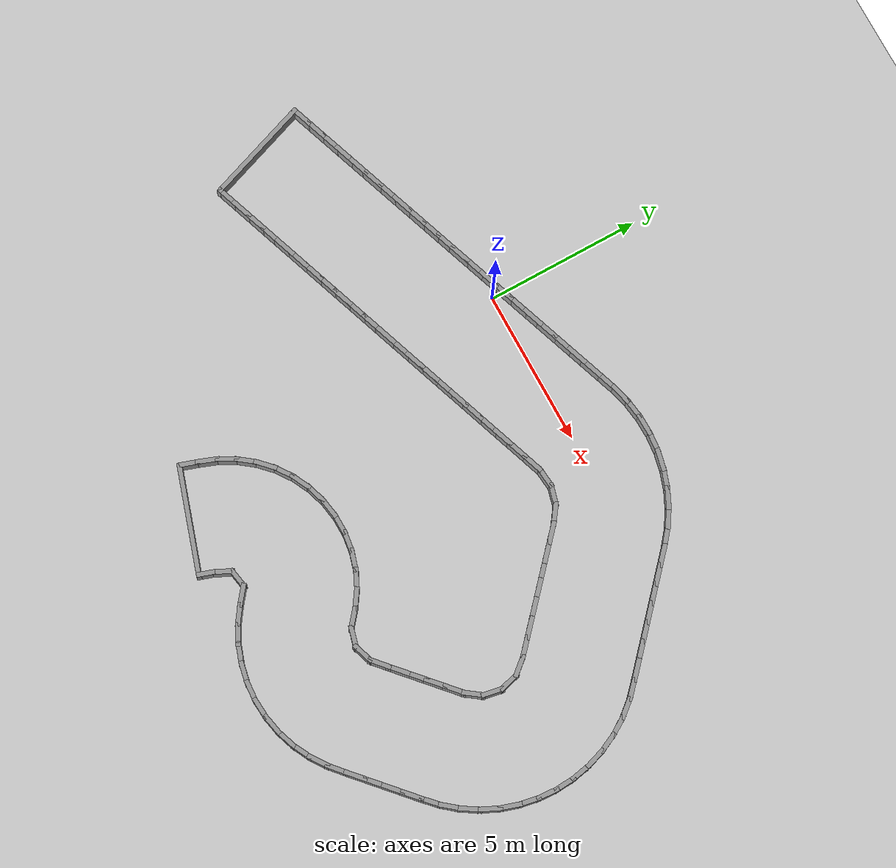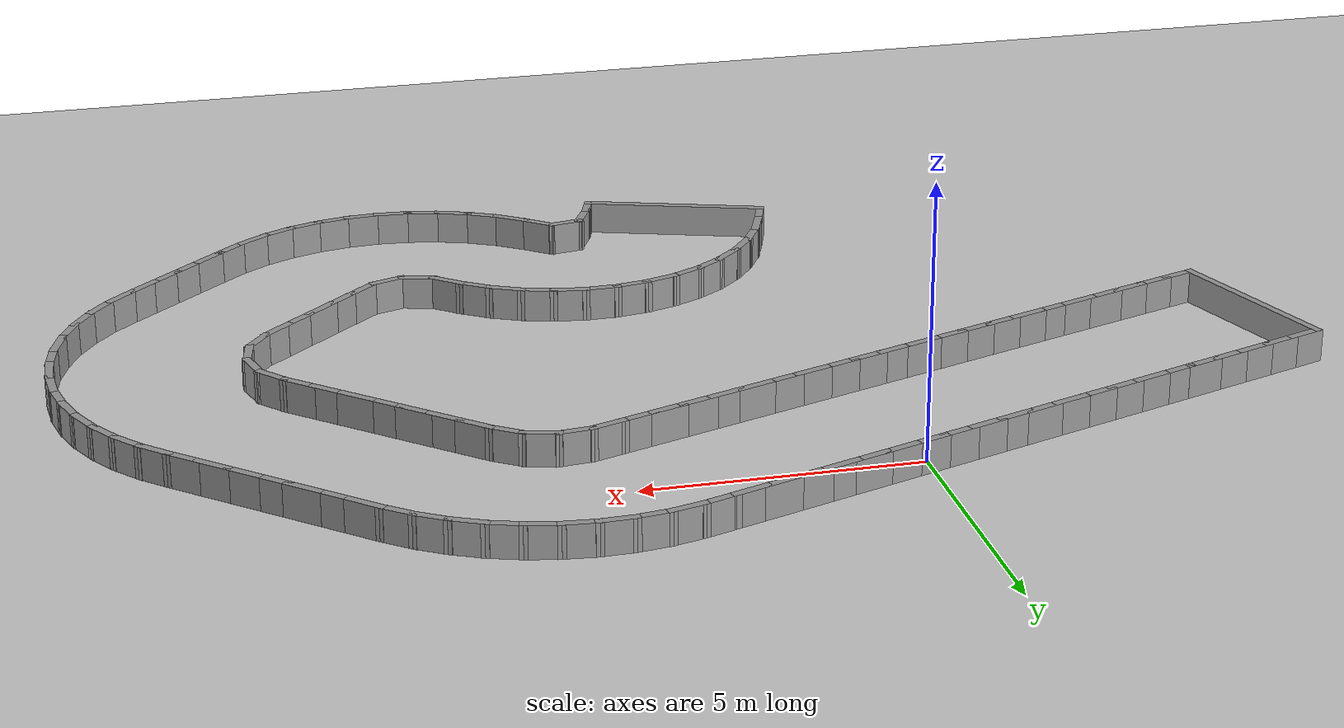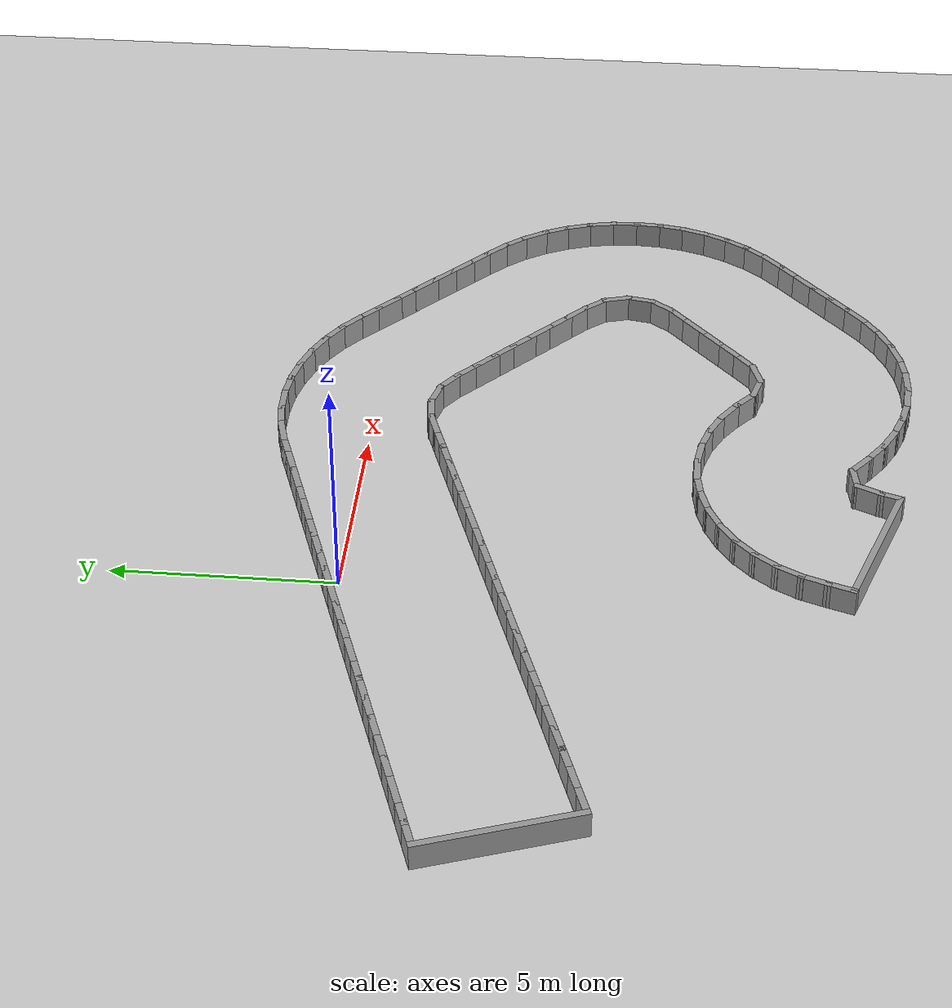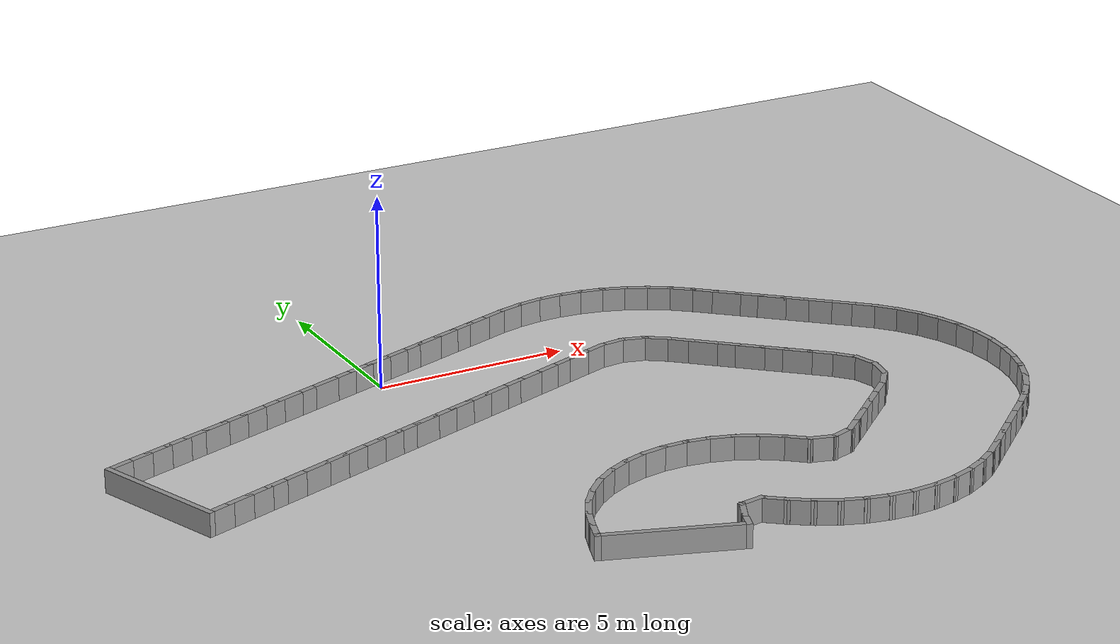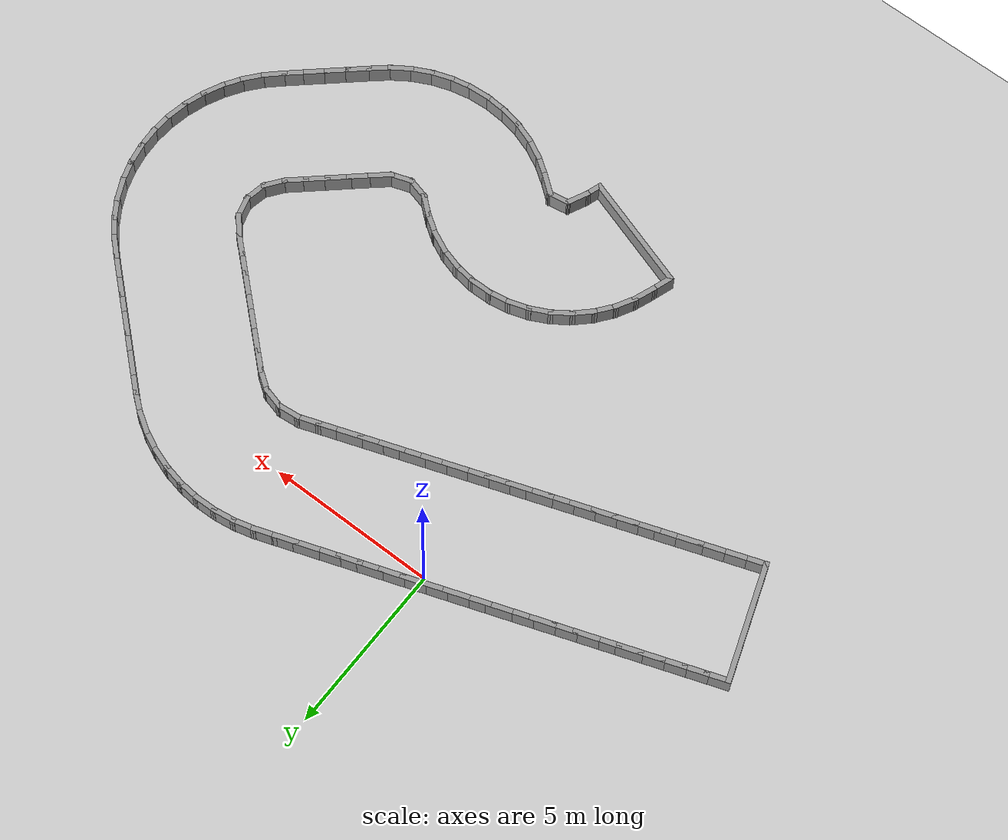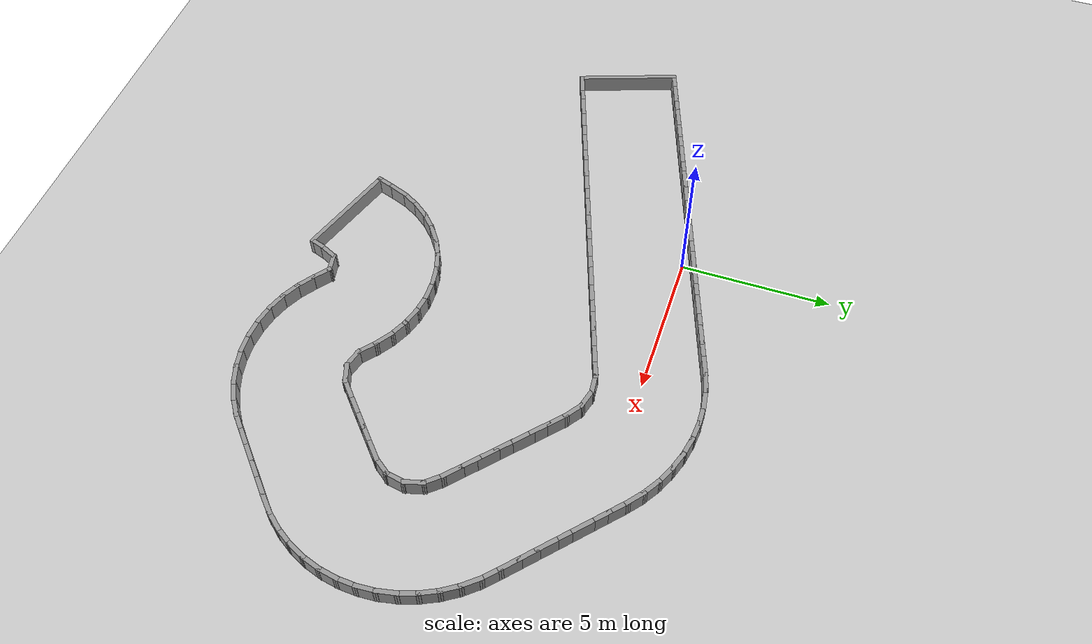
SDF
<?xml version="1.0" ?>
<sdf version='1.7'>
  <world name='default'>
    <plugin name='gazebo_ros_state' filename='libgazebo_ros_state.so'>
      <ros>
        <namespace>/</namespace>
      </ros>
      <update_rate>1000.0</update_rate>
    </plugin>

    <light name='sun' type='directional'>
      <cast_shadows>1</cast_shadows>
      <pose>0 0 10 0 -0 0</pose>
      <diffuse>0.8 0.8 0.8 1</diffuse>
      <specular>0.2 0.2 0.2 1</specular>
      <attenuation>
        <range>1000</range>
        <constant>0.9</constant>
        <linear>0.01</linear>
        <quadratic>0.001</quadratic>
      </attenuation>
      <direction>-0.5 0.1 -0.9</direction>
      <spot>
        <inner_angle>0</inner_angle>
        <outer_angle>0</outer_angle>
        <falloff>0</falloff>
      </spot>
    </light>
    <model name='ground_plane'>
      <static>1</static>
      <link name='link'>
        <collision name='collision'>
          <geometry>
            <plane>
              <normal>0 0 1</normal>
              <size>100 100</size>
            </plane>
          </geometry>
          <surface>
            <friction>
              <ode>
                <mu>100</mu>
                <mu2>50</mu2>
              </ode>
              <torsional>
                <ode/>
              </torsional>
            </friction>
            <contact>
              <ode/>
            </contact>
            <bounce/>
          </surface>
          <max_contacts>10</max_contacts>
        </collision>
        <visual name='visual'>
          <cast_shadows>0</cast_shadows>
          <geometry>
            <plane>
              <normal>0 0 1</normal>
              <size>100 100</size>
            </plane>
          </geometry>
          <material>
            <script>
              <uri>file://media/materials/scripts/gazebo.material</uri>
              <name>Gazebo/Grey</name>
            </script>
          </material>
        </visual>
        <self_collide>0</self_collide>
        <enable_wind>0</enable_wind>
        <kinematic>0</kinematic>
      </link>
    </model>
    <gravity>0 0 -9.8</gravity>
    <magnetic_field>6e-06 2.3e-05 -4.2e-05</magnetic_field>
    <atmosphere type='adiabatic'/>
    <physics type='ode'>
      <max_step_size>0.001</max_step_size>
      <real_time_factor>1</real_time_factor>
      <real_time_update_rate>1000</real_time_update_rate>
    </physics>
    <scene>
      <ambient>0.4 0.4 0.4 1</ambient>
      <background>0.7 0.7 0.7 1</background>
      <shadows>1</shadows>
    </scene>
    <audio>
      <device>default</device>
    </audio>
    <wind/>
    <spherical_coordinates>
      <surface_model>EARTH_WGS84</surface_model>
      <latitude_deg>0</latitude_deg>
      <longitude_deg>0</longitude_deg>
      <elevation>0</elevation>
      <heading_deg>0</heading_deg>
    </spherical_coordinates>
  <model name='rand_turn_08'>
    <pose>0 0 0 0 -0 0</pose>
    <link name='Wall_0'>
      <collision name='Wall_0_Collision'>
        <geometry><box><size>0.7500 0.1500 0.6000</size></box></geometry>
        <pose>0 0 0.3000 0 -0 0</pose>
      </collision>
      <visual name='Wall_0_Visual'>
        <pose>0 0 0.3000 0 -0 0</pose>
        <geometry><box><size>0.7500 0.1500 0.6000</size></box></geometry>
        <material>
          <script>
            <uri>file://media/materials/scripts/gazebo.material</uri>
            <name>Gazebo/Grey</name>
          </script>
          <ambient>1 1 1 1</ambient>
        </material>
      </visual>
      <pose>-7.8536 -2.4259 0 0 -0 0.33717</pose>
    </link>
    <link name='Wall_1'>
      <collision name='Wall_1_Collision'>
        <geometry><box><size>0.7500 0.1500 0.6000</size></box></geometry>
        <pose>0 0 0.3000 0 -0 0</pose>
      </collision>
      <visual name='Wall_1_Visual'>
        <pose>0 0 0.3000 0 -0 0</pose>
        <geometry><box><size>0.7500 0.1500 0.6000</size></box></geometry>
        <material>
          <script>
            <uri>file://media/materials/scripts/gazebo.material</uri>
            <name>Gazebo/Grey</name>
          </script>
          <ambient>1 1 1 1</ambient>
        </material>
      </visual>
      <pose>-7.2874 -2.2274 0 0 -0 0.33717</pose>
    </link>
    <link name='Wall_2'>
      <collision name='Wall_2_Collision'>
        <geometry><box><size>0.7500 0.1500 0.6000</size></box></geometry>
        <pose>0 0 0.3000 0 -0 0</pose>
      </collision>
      <visual name='Wall_2_Visual'>
        <pose>0 0 0.3000 0 -0 0</pose>
        <geometry><box><size>0.7500 0.1500 0.6000</size></box></geometry>
        <material>
          <script>
            <uri>file://media/materials/scripts/gazebo.material</uri>
            <name>Gazebo/Grey</name>
          </script>
          <ambient>1 1 1 1</ambient>
        </material>
      </visual>
      <pose>-6.7212 -2.0289 0 0 -0 0.33717</pose>
    </link>
    <link name='Wall_3'>
      <collision name='Wall_3_Collision'>
        <geometry><box><size>0.7500 0.1500 0.6000</size></box></geometry>
        <pose>0 0 0.3000 0 -0 0</pose>
      </collision>
      <visual name='Wall_3_Visual'>
        <pose>0 0 0.3000 0 -0 0</pose>
        <geometry><box><size>0.7500 0.1500 0.6000</size></box></geometry>
        <material>
          <script>
            <uri>file://media/materials/scripts/gazebo.material</uri>
            <name>Gazebo/Grey</name>
          </script>
          <ambient>1 1 1 1</ambient>
        </material>
      </visual>
      <pose>-6.1550 -1.8304 0 0 -0 0.33717</pose>
    </link>
    <link name='Wall_4'>
      <collision name='Wall_4_Collision'>
        <geometry><box><size>0.7500 0.1500 0.6000</size></box></geometry>
        <pose>0 0 0.3000 0 -0 0</pose>
      </collision>
      <visual name='Wall_4_Visual'>
        <pose>0 0 0.3000 0 -0 0</pose>
        <geometry><box><size>0.7500 0.1500 0.6000</size></box></geometry>
        <material>
          <script>
            <uri>file://media/materials/scripts/gazebo.material</uri>
            <name>Gazebo/Grey</name>
          </script>
          <ambient>1 1 1 1</ambient>
        </material>
      </visual>
      <pose>-5.5888 -1.6319 0 0 -0 0.33717</pose>
    </link>
    <link name='Wall_5'>
      <collision name='Wall_5_Collision'>
        <geometry><box><size>0.7500 0.1500 0.6000</size></box></geometry>
        <pose>0 0 0.3000 0 -0 0</pose>
      </collision>
      <visual name='Wall_5_Visual'>
        <pose>0 0 0.3000 0 -0 0</pose>
        <geometry><box><size>0.7500 0.1500 0.6000</size></box></geometry>
        <material>
          <script>
            <uri>file://media/materials/scripts/gazebo.material</uri>
            <name>Gazebo/Grey</name>
          </script>
          <ambient>1 1 1 1</ambient>
        </material>
      </visual>
      <pose>-5.0225 -1.4335 0 0 -0 0.33717</pose>
    </link>
    <link name='Wall_6'>
      <collision name='Wall_6_Collision'>
        <geometry><box><size>0.7500 0.1500 0.6000</size></box></geometry>
        <pose>0 0 0.3000 0 -0 0</pose>
      </collision>
      <visual name='Wall_6_Visual'>
        <pose>0 0 0.3000 0 -0 0</pose>
        <geometry><box><size>0.7500 0.1500 0.6000</size></box></geometry>
        <material>
          <script>
            <uri>file://media/materials/scripts/gazebo.material</uri>
            <name>Gazebo/Grey</name>
          </script>
          <ambient>1 1 1 1</ambient>
        </material>
      </visual>
      <pose>-4.4563 -1.2350 0 0 -0 0.33717</pose>
    </link>
    <link name='Wall_7'>
      <collision name='Wall_7_Collision'>
        <geometry><box><size>0.7500 0.1500 0.6000</size></box></geometry>
        <pose>0 0 0.3000 0 -0 0</pose>
      </collision>
      <visual name='Wall_7_Visual'>
        <pose>0 0 0.3000 0 -0 0</pose>
        <geometry><box><size>0.7500 0.1500 0.6000</size></box></geometry>
        <material>
          <script>
            <uri>file://media/materials/scripts/gazebo.material</uri>
            <name>Gazebo/Grey</name>
          </script>
          <ambient>1 1 1 1</ambient>
        </material>
      </visual>
      <pose>-3.8901 -1.0365 0 0 -0 0.33717</pose>
    </link>
    <link name='Wall_8'>
      <collision name='Wall_8_Collision'>
        <geometry><box><size>0.7500 0.1500 0.6000</size></box></geometry>
        <pose>0 0 0.3000 0 -0 0</pose>
      </collision>
      <visual name='Wall_8_Visual'>
        <pose>0 0 0.3000 0 -0 0</pose>
        <geometry><box><size>0.7500 0.1500 0.6000</size></box></geometry>
        <material>
          <script>
            <uri>file://media/materials/scripts/gazebo.material</uri>
            <name>Gazebo/Grey</name>
          </script>
          <ambient>1 1 1 1</ambient>
        </material>
      </visual>
      <pose>-3.3239 -0.8380 0 0 -0 0.33717</pose>
    </link>
    <link name='Wall_9'>
      <collision name='Wall_9_Collision'>
        <geometry><box><size>0.7500 0.1500 0.6000</size></box></geometry>
        <pose>0 0 0.3000 0 -0 0</pose>
      </collision>
      <visual name='Wall_9_Visual'>
        <pose>0 0 0.3000 0 -0 0</pose>
        <geometry><box><size>0.7500 0.1500 0.6000</size></box></geometry>
        <material>
          <script>
            <uri>file://media/materials/scripts/gazebo.material</uri>
            <name>Gazebo/Grey</name>
          </script>
          <ambient>1 1 1 1</ambient>
        </material>
      </visual>
      <pose>-2.7577 -0.6395 0 0 -0 0.33717</pose>
    </link>
    <link name='Wall_10'>
      <collision name='Wall_10_Collision'>
        <geometry><box><size>0.7500 0.1500 0.6000</size></box></geometry>
        <pose>0 0 0.3000 0 -0 0</pose>
      </collision>
      <visual name='Wall_10_Visual'>
        <pose>0 0 0.3000 0 -0 0</pose>
        <geometry><box><size>0.7500 0.1500 0.6000</size></box></geometry>
        <material>
          <script>
            <uri>file://media/materials/scripts/gazebo.material</uri>
            <name>Gazebo/Grey</name>
          </script>
          <ambient>1 1 1 1</ambient>
        </material>
      </visual>
      <pose>-2.1915 -0.4410 0 0 -0 0.33717</pose>
    </link>
    <link name='Wall_11'>
      <collision name='Wall_11_Collision'>
        <geometry><box><size>0.7500 0.1500 0.6000</size></box></geometry>
        <pose>0 0 0.3000 0 -0 0</pose>
      </collision>
      <visual name='Wall_11_Visual'>
        <pose>0 0 0.3000 0 -0 0</pose>
        <geometry><box><size>0.7500 0.1500 0.6000</size></box></geometry>
        <material>
          <script>
            <uri>file://media/materials/scripts/gazebo.material</uri>
            <name>Gazebo/Grey</name>
          </script>
          <ambient>1 1 1 1</ambient>
        </material>
      </visual>
      <pose>-1.6252 -0.2425 0 0 -0 0.33717</pose>
    </link>
    <link name='Wall_12'>
      <collision name='Wall_12_Collision'>
        <geometry><box><size>0.7500 0.1500 0.6000</size></box></geometry>
        <pose>0 0 0.3000 0 -0 0</pose>
      </collision>
      <visual name='Wall_12_Visual'>
        <pose>0 0 0.3000 0 -0 0</pose>
        <geometry><box><size>0.7500 0.1500 0.6000</size></box></geometry>
        <material>
          <script>
            <uri>file://media/materials/scripts/gazebo.material</uri>
            <name>Gazebo/Grey</name>
          </script>
          <ambient>1 1 1 1</ambient>
        </material>
      </visual>
      <pose>-1.0590 -0.0440 0 0 -0 0.33717</pose>
    </link>
    <link name='Wall_13'>
      <collision name='Wall_13_Collision'>
        <geometry><box><size>0.7500 0.1500 0.6000</size></box></geometry>
        <pose>0 0 0.3000 0 -0 0</pose>
      </collision>
      <visual name='Wall_13_Visual'>
        <pose>0 0 0.3000 0 -0 0</pose>
        <geometry><box><size>0.7500 0.1500 0.6000</size></box></geometry>
        <material>
          <script>
            <uri>file://media/materials/scripts/gazebo.material</uri>
            <name>Gazebo/Grey</name>
          </script>
          <ambient>1 1 1 1</ambient>
        </material>
      </visual>
      <pose>-0.4928 0.1545 0 0 -0 0.33717</pose>
    </link>
    <link name='Wall_14'>
      <collision name='Wall_14_Collision'>
        <geometry><box><size>0.7500 0.1500 0.6000</size></box></geometry>
        <pose>0 0 0.3000 0 -0 0</pose>
      </collision>
      <visual name='Wall_14_Visual'>
        <pose>0 0 0.3000 0 -0 0</pose>
        <geometry><box><size>0.7500 0.1500 0.6000</size></box></geometry>
        <material>
          <script>
            <uri>file://media/materials/scripts/gazebo.material</uri>
            <name>Gazebo/Grey</name>
          </script>
          <ambient>1 1 1 1</ambient>
        </material>
      </visual>
      <pose>0.0734 0.3530 0 0 -0 0.33717</pose>
    </link>
    <link name='Wall_15'>
      <collision name='Wall_15_Collision'>
        <geometry><box><size>0.7500 0.1500 0.6000</size></box></geometry>
        <pose>0 0 0.3000 0 -0 0</pose>
      </collision>
      <visual name='Wall_15_Visual'>
        <pose>0 0 0.3000 0 -0 0</pose>
        <geometry><box><size>0.7500 0.1500 0.6000</size></box></geometry>
        <material>
          <script>
            <uri>file://media/materials/scripts/gazebo.material</uri>
            <name>Gazebo/Grey</name>
          </script>
          <ambient>1 1 1 1</ambient>
        </material>
      </visual>
      <pose>0.6396 0.5515 0 0 -0 0.33717</pose>
    </link>
    <link name='Wall_16'>
      <collision name='Wall_16_Collision'>
        <geometry><box><size>0.7500 0.1500 0.6000</size></box></geometry>
        <pose>0 0 0.3000 0 -0 0</pose>
      </collision>
      <visual name='Wall_16_Visual'>
        <pose>0 0 0.3000 0 -0 0</pose>
        <geometry><box><size>0.7500 0.1500 0.6000</size></box></geometry>
        <material>
          <script>
            <uri>file://media/materials/scripts/gazebo.material</uri>
            <name>Gazebo/Grey</name>
          </script>
          <ambient>1 1 1 1</ambient>
        </material>
      </visual>
      <pose>1.2058 0.7500 0 0 -0 0.33717</pose>
    </link>
    <link name='Wall_17'>
      <collision name='Wall_17_Collision'>
        <geometry><box><size>0.7500 0.1500 0.6000</size></box></geometry>
        <pose>0 0 0.3000 0 -0 0</pose>
      </collision>
      <visual name='Wall_17_Visual'>
        <pose>0 0 0.3000 0 -0 0</pose>
        <geometry><box><size>0.7500 0.1500 0.6000</size></box></geometry>
        <material>
          <script>
            <uri>file://media/materials/scripts/gazebo.material</uri>
            <name>Gazebo/Grey</name>
          </script>
          <ambient>1 1 1 1</ambient>
        </material>
      </visual>
      <pose>1.7721 0.9485 0 0 -0 0.33717</pose>
    </link>
    <link name='Wall_18'>
      <collision name='Wall_18_Collision'>
        <geometry><box><size>0.7500 0.1500 0.6000</size></box></geometry>
        <pose>0 0 0.3000 0 -0 0</pose>
      </collision>
      <visual name='Wall_18_Visual'>
        <pose>0 0 0.3000 0 -0 0</pose>
        <geometry><box><size>0.7500 0.1500 0.6000</size></box></geometry>
        <material>
          <script>
            <uri>file://media/materials/scripts/gazebo.material</uri>
            <name>Gazebo/Grey</name>
          </script>
          <ambient>1 1 1 1</ambient>
        </material>
      </visual>
      <pose>2.3383 1.1470 0 0 -0 0.33717</pose>
    </link>
    <link name='Wall_19'>
      <collision name='Wall_19_Collision'>
        <geometry><box><size>0.7500 0.1500 0.6000</size></box></geometry>
        <pose>0 0 0.3000 0 -0 0</pose>
      </collision>
      <visual name='Wall_19_Visual'>
        <pose>0 0 0.3000 0 -0 0</pose>
        <geometry><box><size>0.7500 0.1500 0.6000</size></box></geometry>
        <material>
          <script>
            <uri>file://media/materials/scripts/gazebo.material</uri>
            <name>Gazebo/Grey</name>
          </script>
          <ambient>1 1 1 1</ambient>
        </material>
      </visual>
      <pose>2.9045 1.3455 0 0 -0 0.33717</pose>
    </link>
    <link name='Wall_20'>
      <collision name='Wall_20_Collision'>
        <geometry><box><size>0.7500 0.1500 0.6000</size></box></geometry>
        <pose>0 0 0.3000 0 -0 0</pose>
      </collision>
      <visual name='Wall_20_Visual'>
        <pose>0 0 0.3000 0 -0 0</pose>
        <geometry><box><size>0.7500 0.1500 0.6000</size></box></geometry>
        <material>
          <script>
            <uri>file://media/materials/scripts/gazebo.material</uri>
            <name>Gazebo/Grey</name>
          </script>
          <ambient>1 1 1 1</ambient>
        </material>
      </visual>
      <pose>3.4707 1.5439 0 0 -0 0.33717</pose>
    </link>
    <link name='Wall_21'>
      <collision name='Wall_21_Collision'>
        <geometry><box><size>0.7500 0.1500 0.6000</size></box></geometry>
        <pose>0 0 0.3000 0 -0 0</pose>
      </collision>
      <visual name='Wall_21_Visual'>
        <pose>0 0 0.3000 0 -0 0</pose>
        <geometry><box><size>0.7500 0.1500 0.6000</size></box></geometry>
        <material>
          <script>
            <uri>file://media/materials/scripts/gazebo.material</uri>
            <name>Gazebo/Grey</name>
          </script>
          <ambient>1 1 1 1</ambient>
        </material>
      </visual>
      <pose>4.0371 1.7418 0 0 -0 0.33480</pose>
    </link>
    <link name='Wall_22'>
      <collision name='Wall_22_Collision'>
        <geometry><box><size>0.7496 0.1500 0.6000</size></box></geometry>
        <pose>0 0 0.3000 0 -0 0</pose>
      </collision>
      <visual name='Wall_22_Visual'>
        <pose>0 0 0.3000 0 -0 0</pose>
        <geometry><box><size>0.7496 0.1500 0.6000</size></box></geometry>
        <material>
          <script>
            <uri>file://media/materials/scripts/gazebo.material</uri>
            <name>Gazebo/Grey</name>
          </script>
          <ambient>1 1 1 1</ambient>
        </material>
      </visual>
      <pose>4.6103 1.9170 0 0 -0 0.25872</pose>
    </link>
    <link name='Wall_23'>
      <collision name='Wall_23_Collision'>
        <geometry><box><size>0.7496 0.1500 0.6000</size></box></geometry>
        <pose>0 0 0.3000 0 -0 0</pose>
      </collision>
      <visual name='Wall_23_Visual'>
        <pose>0 0 0.3000 0 -0 0</pose>
        <geometry><box><size>0.7496 0.1500 0.6000</size></box></geometry>
        <material>
          <script>
            <uri>file://media/materials/scripts/gazebo.material</uri>
            <name>Gazebo/Grey</name>
          </script>
          <ambient>1 1 1 1</ambient>
        </material>
      </visual>
      <pose>5.1970 2.0360 0 0 -0 0.14129</pose>
    </link>
    <link name='Wall_24'>
      <collision name='Wall_24_Collision'>
        <geometry><box><size>0.7496 0.1500 0.6000</size></box></geometry>
        <pose>0 0 0.3000 0 -0 0</pose>
      </collision>
      <visual name='Wall_24_Visual'>
        <pose>0 0 0.3000 0 -0 0</pose>
        <geometry><box><size>0.7496 0.1500 0.6000</size></box></geometry>
        <material>
          <script>
            <uri>file://media/materials/scripts/gazebo.material</uri>
            <name>Gazebo/Grey</name>
          </script>
          <ambient>1 1 1 1</ambient>
        </material>
      </visual>
      <pose>5.7935 2.0853 0 0 -0 0.02378</pose>
    </link>
    <link name='Wall_25'>
      <collision name='Wall_25_Collision'>
        <geometry><box><size>0.7496 0.1500 0.6000</size></box></geometry>
        <pose>0 0 0.3000 0 -0 0</pose>
      </collision>
      <visual name='Wall_25_Visual'>
        <pose>0 0 0.3000 0 -0 0</pose>
        <geometry><box><size>0.7496 0.1500 0.6000</size></box></geometry>
        <material>
          <script>
            <uri>file://media/materials/scripts/gazebo.material</uri>
            <name>Gazebo/Grey</name>
          </script>
          <ambient>1 1 1 1</ambient>
        </material>
      </visual>
      <pose>6.3917 2.0644 0 0 -0 -0.09374</pose>
    </link>
    <link name='Wall_26'>
      <collision name='Wall_26_Collision'>
        <geometry><box><size>0.7496 0.1500 0.6000</size></box></geometry>
        <pose>0 0 0.3000 0 -0 0</pose>
      </collision>
      <visual name='Wall_26_Visual'>
        <pose>0 0 0.3000 0 -0 0</pose>
        <geometry><box><size>0.7496 0.1500 0.6000</size></box></geometry>
        <material>
          <script>
            <uri>file://media/materials/scripts/gazebo.material</uri>
            <name>Gazebo/Grey</name>
          </script>
          <ambient>1 1 1 1</ambient>
        </material>
      </visual>
      <pose>6.9834 1.9735 0 0 -0 -0.21125</pose>
    </link>
    <link name='Wall_27'>
      <collision name='Wall_27_Collision'>
        <geometry><box><size>0.7496 0.1500 0.6000</size></box></geometry>
        <pose>0 0 0.3000 0 -0 0</pose>
      </collision>
      <visual name='Wall_27_Visual'>
        <pose>0 0 0.3000 0 -0 0</pose>
        <geometry><box><size>0.7496 0.1500 0.6000</size></box></geometry>
        <material>
          <script>
            <uri>file://media/materials/scripts/gazebo.material</uri>
            <name>Gazebo/Grey</name>
          </script>
          <ambient>1 1 1 1</ambient>
        </material>
      </visual>
      <pose>7.5602 1.8138 0 0 -0 -0.32876</pose>
    </link>
    <link name='Wall_28'>
      <collision name='Wall_28_Collision'>
        <geometry><box><size>0.7496 0.1500 0.6000</size></box></geometry>
        <pose>0 0 0.3000 0 -0 0</pose>
      </collision>
      <visual name='Wall_28_Visual'>
        <pose>0 0 0.3000 0 -0 0</pose>
        <geometry><box><size>0.7496 0.1500 0.6000</size></box></geometry>
        <material>
          <script>
            <uri>file://media/materials/scripts/gazebo.material</uri>
            <name>Gazebo/Grey</name>
          </script>
          <ambient>1 1 1 1</ambient>
        </material>
      </visual>
      <pose>8.1144 1.5876 0 0 -0 -0.44628</pose>
    </link>
    <link name='Wall_29'>
      <collision name='Wall_29_Collision'>
        <geometry><box><size>0.7496 0.1500 0.6000</size></box></geometry>
        <pose>0 0 0.3000 0 -0 0</pose>
      </collision>
      <visual name='Wall_29_Visual'>
        <pose>0 0 0.3000 0 -0 0</pose>
        <geometry><box><size>0.7496 0.1500 0.6000</size></box></geometry>
        <material>
          <script>
            <uri>file://media/materials/scripts/gazebo.material</uri>
            <name>Gazebo/Grey</name>
          </script>
          <ambient>1 1 1 1</ambient>
        </material>
      </visual>
      <pose>8.6383 1.2980 0 0 -0 -0.56379</pose>
    </link>
    <link name='Wall_30'>
      <collision name='Wall_30_Collision'>
        <geometry><box><size>0.7496 0.1500 0.6000</size></box></geometry>
        <pose>0 0 0.3000 0 -0 0</pose>
      </collision>
      <visual name='Wall_30_Visual'>
        <pose>0 0 0.3000 0 -0 0</pose>
        <geometry><box><size>0.7496 0.1500 0.6000</size></box></geometry>
        <material>
          <script>
            <uri>file://media/materials/scripts/gazebo.material</uri>
            <name>Gazebo/Grey</name>
          </script>
          <ambient>1 1 1 1</ambient>
        </material>
      </visual>
      <pose>9.1247 0.9491 0 0 -0 -0.68079</pose>
    </link>
    <link name='Wall_31'>
      <collision name='Wall_31_Collision'>
        <geometry><box><size>0.7500 0.1500 0.6000</size></box></geometry>
        <pose>0 0 0.3000 0 -0 0</pose>
      </collision>
      <visual name='Wall_31_Visual'>
        <pose>0 0 0.3000 0 -0 0</pose>
        <geometry><box><size>0.7500 0.1500 0.6000</size></box></geometry>
        <material>
          <script>
            <uri>file://media/materials/scripts/gazebo.material</uri>
            <name>Gazebo/Grey</name>
          </script>
          <ambient>1 1 1 1</ambient>
        </material>
      </visual>
      <pose>9.5798 0.5588 0 0 -0 -0.73675</pose>
    </link>
    <link name='Wall_32'>
      <collision name='Wall_32_Collision'>
        <geometry><box><size>0.7500 0.1500 0.6000</size></box></geometry>
        <pose>0 0 0.3000 0 -0 0</pose>
      </collision>
      <visual name='Wall_32_Visual'>
        <pose>0 0 0.3000 0 -0 0</pose>
        <geometry><box><size>0.7500 0.1500 0.6000</size></box></geometry>
        <material>
          <script>
            <uri>file://media/materials/scripts/gazebo.material</uri>
            <name>Gazebo/Grey</name>
          </script>
          <ambient>1 1 1 1</ambient>
        </material>
      </visual>
      <pose>10.0242 0.1556 0 0 -0 -0.73684</pose>
    </link>
    <link name='Wall_33'>
      <collision name='Wall_33_Collision'>
        <geometry><box><size>0.7500 0.1500 0.6000</size></box></geometry>
        <pose>0 0 0.3000 0 -0 0</pose>
      </collision>
      <visual name='Wall_33_Visual'>
        <pose>0 0 0.3000 0 -0 0</pose>
        <geometry><box><size>0.7500 0.1500 0.6000</size></box></geometry>
        <material>
          <script>
            <uri>file://media/materials/scripts/gazebo.material</uri>
            <name>Gazebo/Grey</name>
          </script>
          <ambient>1 1 1 1</ambient>
        </material>
      </visual>
      <pose>10.4686 -0.2475 0 0 -0 -0.73684</pose>
    </link>
    <link name='Wall_34'>
      <collision name='Wall_34_Collision'>
        <geometry><box><size>0.7500 0.1500 0.6000</size></box></geometry>
        <pose>0 0 0.3000 0 -0 0</pose>
      </collision>
      <visual name='Wall_34_Visual'>
        <pose>0 0 0.3000 0 -0 0</pose>
        <geometry><box><size>0.7500 0.1500 0.6000</size></box></geometry>
        <material>
          <script>
            <uri>file://media/materials/scripts/gazebo.material</uri>
            <name>Gazebo/Grey</name>
          </script>
          <ambient>1 1 1 1</ambient>
        </material>
      </visual>
      <pose>10.9129 -0.6507 0 0 -0 -0.73684</pose>
    </link>
    <link name='Wall_35'>
      <collision name='Wall_35_Collision'>
        <geometry><box><size>0.7500 0.1500 0.6000</size></box></geometry>
        <pose>0 0 0.3000 0 -0 0</pose>
      </collision>
      <visual name='Wall_35_Visual'>
        <pose>0 0 0.3000 0 -0 0</pose>
        <geometry><box><size>0.7500 0.1500 0.6000</size></box></geometry>
        <material>
          <script>
            <uri>file://media/materials/scripts/gazebo.material</uri>
            <name>Gazebo/Grey</name>
          </script>
          <ambient>1 1 1 1</ambient>
        </material>
      </visual>
      <pose>11.3573 -1.0539 0 0 -0 -0.73684</pose>
    </link>
    <link name='Wall_36'>
      <collision name='Wall_36_Collision'>
        <geometry><box><size>0.7500 0.1500 0.6000</size></box></geometry>
        <pose>0 0 0.3000 0 -0 0</pose>
      </collision>
      <visual name='Wall_36_Visual'>
        <pose>0 0 0.3000 0 -0 0</pose>
        <geometry><box><size>0.7500 0.1500 0.6000</size></box></geometry>
        <material>
          <script>
            <uri>file://media/materials/scripts/gazebo.material</uri>
            <name>Gazebo/Grey</name>
          </script>
          <ambient>1 1 1 1</ambient>
        </material>
      </visual>
      <pose>11.8016 -1.4570 0 0 -0 -0.73684</pose>
    </link>
    <link name='Wall_37'>
      <collision name='Wall_37_Collision'>
        <geometry><box><size>0.7500 0.1500 0.6000</size></box></geometry>
        <pose>0 0 0.3000 0 -0 0</pose>
      </collision>
      <visual name='Wall_37_Visual'>
        <pose>0 0 0.3000 0 -0 0</pose>
        <geometry><box><size>0.7500 0.1500 0.6000</size></box></geometry>
        <material>
          <script>
            <uri>file://media/materials/scripts/gazebo.material</uri>
            <name>Gazebo/Grey</name>
          </script>
          <ambient>1 1 1 1</ambient>
        </material>
      </visual>
      <pose>12.2460 -1.8602 0 0 -0 -0.73684</pose>
    </link>
    <link name='Wall_38'>
      <collision name='Wall_38_Collision'>
        <geometry><box><size>0.7498 0.1500 0.6000</size></box></geometry>
        <pose>0 0 0.3000 0 -0 0</pose>
      </collision>
      <visual name='Wall_38_Visual'>
        <pose>0 0 0.3000 0 -0 0</pose>
        <geometry><box><size>0.7498 0.1500 0.6000</size></box></geometry>
        <material>
          <script>
            <uri>file://media/materials/scripts/gazebo.material</uri>
            <name>Gazebo/Grey</name>
          </script>
          <ambient>1 1 1 1</ambient>
        </material>
      </visual>
      <pose>12.6856 -2.2684 0 0 -0 -0.75972</pose>
    </link>
    <link name='Wall_39'>
      <collision name='Wall_39_Collision'>
        <geometry><box><size>0.7496 0.1500 0.6000</size></box></geometry>
        <pose>0 0 0.3000 0 -0 0</pose>
      </collision>
      <visual name='Wall_39_Visual'>
        <pose>0 0 0.3000 0 -0 0</pose>
        <geometry><box><size>0.7496 0.1500 0.6000</size></box></geometry>
        <material>
          <script>
            <uri>file://media/materials/scripts/gazebo.material</uri>
            <name>Gazebo/Grey</name>
          </script>
          <ambient>1 1 1 1</ambient>
        </material>
      </visual>
      <pose>13.0955 -2.7048 0 0 -0 -0.87392</pose>
    </link>
    <link name='Wall_40'>
      <collision name='Wall_40_Collision'>
        <geometry><box><size>0.7496 0.1500 0.6000</size></box></geometry>
        <pose>0 0 0.3000 0 -0 0</pose>
      </collision>
      <visual name='Wall_40_Visual'>
        <pose>0 0 0.3000 0 -0 0</pose>
        <geometry><box><size>0.7496 0.1500 0.6000</size></box></geometry>
        <material>
          <script>
            <uri>file://media/materials/scripts/gazebo.material</uri>
            <name>Gazebo/Grey</name>
          </script>
          <ambient>1 1 1 1</ambient>
        </material>
      </visual>
      <pose>13.4498 -3.1870 0 0 -0 -1.00021</pose>
    </link>
    <link name='Wall_41'>
      <collision name='Wall_41_Collision'>
        <geometry><box><size>0.7496 0.1500 0.6000</size></box></geometry>
        <pose>0 0 0.3000 0 -0 0</pose>
      </collision>
      <visual name='Wall_41_Visual'>
        <pose>0 0 0.3000 0 -0 0</pose>
        <geometry><box><size>0.7496 0.1500 0.6000</size></box></geometry>
        <material>
          <script>
            <uri>file://media/materials/scripts/gazebo.material</uri>
            <name>Gazebo/Grey</name>
          </script>
          <ambient>1 1 1 1</ambient>
        </material>
      </visual>
      <pose>13.7405 -3.7101 0 0 -0 -1.12687</pose>
    </link>
    <link name='Wall_42'>
      <collision name='Wall_42_Collision'>
        <geometry><box><size>0.7496 0.1500 0.6000</size></box></geometry>
        <pose>0 0 0.3000 0 -0 0</pose>
      </collision>
      <visual name='Wall_42_Visual'>
        <pose>0 0 0.3000 0 -0 0</pose>
        <geometry><box><size>0.7496 0.1500 0.6000</size></box></geometry>
        <material>
          <script>
            <uri>file://media/materials/scripts/gazebo.material</uri>
            <name>Gazebo/Grey</name>
          </script>
          <ambient>1 1 1 1</ambient>
        </material>
      </visual>
      <pose>13.9630 -4.2655 0 0 -0 -1.25264</pose>
    </link>
    <link name='Wall_43'>
      <collision name='Wall_43_Collision'>
        <geometry><box><size>0.7495 0.1500 0.6000</size></box></geometry>
        <pose>0 0 0.3000 0 -0 0</pose>
      </collision>
      <visual name='Wall_43_Visual'>
        <pose>0 0 0.3000 0 -0 0</pose>
        <geometry><box><size>0.7495 0.1500 0.6000</size></box></geometry>
        <material>
          <script>
            <uri>file://media/materials/scripts/gazebo.material</uri>
            <name>Gazebo/Grey</name>
          </script>
          <ambient>1 1 1 1</ambient>
        </material>
      </visual>
      <pose>14.1141 -4.8445 0 0 -0 -1.37841</pose>
    </link>
    <link name='Wall_44'>
      <collision name='Wall_44_Collision'>
        <geometry><box><size>0.7496 0.1500 0.6000</size></box></geometry>
        <pose>0 0 0.3000 0 -0 0</pose>
      </collision>
      <visual name='Wall_44_Visual'>
        <pose>0 0 0.3000 0 -0 0</pose>
        <geometry><box><size>0.7496 0.1500 0.6000</size></box></geometry>
        <material>
          <script>
            <uri>file://media/materials/scripts/gazebo.material</uri>
            <name>Gazebo/Grey</name>
          </script>
          <ambient>1 1 1 1</ambient>
        </material>
      </visual>
      <pose>14.1914 -5.4379 0 0 -0 -1.50417</pose>
    </link>
    <link name='Wall_45'>
      <collision name='Wall_45_Collision'>
        <geometry><box><size>0.7496 0.1500 0.6000</size></box></geometry>
        <pose>0 0 0.3000 0 -0 0</pose>
      </collision>
      <visual name='Wall_45_Visual'>
        <pose>0 0 0.3000 0 -0 0</pose>
        <geometry><box><size>0.7496 0.1500 0.6000</size></box></geometry>
        <material>
          <script>
            <uri>file://media/materials/scripts/gazebo.material</uri>
            <name>Gazebo/Grey</name>
          </script>
          <ambient>1 1 1 1</ambient>
        </material>
      </visual>
      <pose>14.1936 -6.0362 0 0 -0 -1.62994</pose>
    </link>
    <link name='Wall_46'>
      <collision name='Wall_46_Collision'>
        <geometry><box><size>0.7496 0.1500 0.6000</size></box></geometry>
        <pose>0 0 0.3000 0 -0 0</pose>
      </collision>
      <visual name='Wall_46_Visual'>
        <pose>0 0 0.3000 0 -0 0</pose>
        <geometry><box><size>0.7496 0.1500 0.6000</size></box></geometry>
        <material>
          <script>
            <uri>file://media/materials/scripts/gazebo.material</uri>
            <name>Gazebo/Grey</name>
          </script>
          <ambient>1 1 1 1</ambient>
        </material>
      </visual>
      <pose>14.1207 -6.6302 0 0 -0 -1.75612</pose>
    </link>
    <link name='Wall_47'>
      <collision name='Wall_47_Collision'>
        <geometry><box><size>0.7496 0.1500 0.6000</size></box></geometry>
        <pose>0 0 0.3000 0 -0 0</pose>
      </collision>
      <visual name='Wall_47_Visual'>
        <pose>0 0 0.3000 0 -0 0</pose>
        <geometry><box><size>0.7496 0.1500 0.6000</size></box></geometry>
        <material>
          <script>
            <uri>file://media/materials/scripts/gazebo.material</uri>
            <name>Gazebo/Grey</name>
          </script>
          <ambient>1 1 1 1</ambient>
        </material>
      </visual>
      <pose>13.9734 -7.2102 0 0 -0 -1.88289</pose>
    </link>
    <link name='Wall_48'>
      <collision name='Wall_48_Collision'>
        <geometry><box><size>0.7496 0.1500 0.6000</size></box></geometry>
        <pose>0 0 0.3000 0 -0 0</pose>
      </collision>
      <visual name='Wall_48_Visual'>
        <pose>0 0 0.3000 0 -0 0</pose>
        <geometry><box><size>0.7496 0.1500 0.6000</size></box></geometry>
        <material>
          <script>
            <uri>file://media/materials/scripts/gazebo.material</uri>
            <name>Gazebo/Grey</name>
          </script>
          <ambient>1 1 1 1</ambient>
        </material>
      </visual>
      <pose>13.7542 -7.7670 0 0 -0 -2.00865</pose>
    </link>
    <link name='Wall_49'>
      <collision name='Wall_49_Collision'>
        <geometry><box><size>0.7495 0.1500 0.6000</size></box></geometry>
        <pose>0 0 0.3000 0 -0 0</pose>
      </collision>
      <visual name='Wall_49_Visual'>
        <pose>0 0 0.3000 0 -0 0</pose>
        <geometry><box><size>0.7495 0.1500 0.6000</size></box></geometry>
        <material>
          <script>
            <uri>file://media/materials/scripts/gazebo.material</uri>
            <name>Gazebo/Grey</name>
          </script>
          <ambient>1 1 1 1</ambient>
        </material>
      </visual>
      <pose>13.4670 -8.2919 0 0 -0 -2.13442</pose>
    </link>
    <link name='Wall_50'>
      <collision name='Wall_50_Collision'>
        <geometry><box><size>0.7496 0.1500 0.6000</size></box></geometry>
        <pose>0 0 0.3000 0 -0 0</pose>
      </collision>
      <visual name='Wall_50_Visual'>
        <pose>0 0 0.3000 0 -0 0</pose>
        <geometry><box><size>0.7496 0.1500 0.6000</size></box></geometry>
        <material>
          <script>
            <uri>file://media/materials/scripts/gazebo.material</uri>
            <name>Gazebo/Grey</name>
          </script>
          <ambient>1 1 1 1</ambient>
        </material>
      </visual>
      <pose>13.1161 -8.7766 0 0 -0 -2.26019</pose>
    </link>
    <link name='Wall_51'>
      <collision name='Wall_51_Collision'>
        <geometry><box><size>0.7497 0.1500 0.6000</size></box></geometry>
        <pose>0 0 0.3000 0 -0 0</pose>
      </collision>
      <visual name='Wall_51_Visual'>
        <pose>0 0 0.3000 0 -0 0</pose>
        <geometry><box><size>0.7497 0.1500 0.6000</size></box></geometry>
        <material>
          <script>
            <uri>file://media/materials/scripts/gazebo.material</uri>
            <name>Gazebo/Grey</name>
          </script>
          <ambient>1 1 1 1</ambient>
        </material>
      </visual>
      <pose>12.7081 -9.2145 0 0 -0 -2.38179</pose>
    </link>
    <link name='Wall_52'>
      <collision name='Wall_52_Collision'>
        <geometry><box><size>0.7500 0.1500 0.6000</size></box></geometry>
        <pose>0 0 0.3000 0 -0 0</pose>
      </collision>
      <visual name='Wall_52_Visual'>
        <pose>0 0 0.3000 0 -0 0</pose>
        <geometry><box><size>0.7500 0.1500 0.6000</size></box></geometry>
        <material>
          <script>
            <uri>file://media/materials/scripts/gazebo.material</uri>
            <name>Gazebo/Grey</name>
          </script>
          <ambient>1 1 1 1</ambient>
        </material>
      </visual>
      <pose>12.2674 -9.6214 0 0 -0 -2.41018</pose>
    </link>
    <link name='Wall_53'>
      <collision name='Wall_53_Collision'>
        <geometry><box><size>0.7500 0.1500 0.6000</size></box></geometry>
        <pose>0 0 0.3000 0 -0 0</pose>
      </collision>
      <visual name='Wall_53_Visual'>
        <pose>0 0 0.3000 0 -0 0</pose>
        <geometry><box><size>0.7500 0.1500 0.6000</size></box></geometry>
        <material>
          <script>
            <uri>file://media/materials/scripts/gazebo.material</uri>
            <name>Gazebo/Grey</name>
          </script>
          <ambient>1 1 1 1</ambient>
        </material>
      </visual>
      <pose>11.8209 -10.0221 0 0 -0 -2.41018</pose>
    </link>
    <link name='Wall_54'>
      <collision name='Wall_54_Collision'>
        <geometry><box><size>0.7500 0.1500 0.6000</size></box></geometry>
        <pose>0 0 0.3000 0 -0 0</pose>
      </collision>
      <visual name='Wall_54_Visual'>
        <pose>0 0 0.3000 0 -0 0</pose>
        <geometry><box><size>0.7500 0.1500 0.6000</size></box></geometry>
        <material>
          <script>
            <uri>file://media/materials/scripts/gazebo.material</uri>
            <name>Gazebo/Grey</name>
          </script>
          <ambient>1 1 1 1</ambient>
        </material>
      </visual>
      <pose>11.3743 -10.4229 0 0 -0 -2.41018</pose>
    </link>
    <link name='Wall_55'>
      <collision name='Wall_55_Collision'>
        <geometry><box><size>0.7500 0.1500 0.6000</size></box></geometry>
        <pose>0 0 0.3000 0 -0 0</pose>
      </collision>
      <visual name='Wall_55_Visual'>
        <pose>0 0 0.3000 0 -0 0</pose>
        <geometry><box><size>0.7500 0.1500 0.6000</size></box></geometry>
        <material>
          <script>
            <uri>file://media/materials/scripts/gazebo.material</uri>
            <name>Gazebo/Grey</name>
          </script>
          <ambient>1 1 1 1</ambient>
        </material>
      </visual>
      <pose>10.9278 -10.8236 0 0 -0 -2.41018</pose>
    </link>
    <link name='Wall_56'>
      <collision name='Wall_56_Collision'>
        <geometry><box><size>0.7499 0.1500 0.6000</size></box></geometry>
        <pose>0 0 0.3000 0 -0 0</pose>
      </collision>
      <visual name='Wall_56_Visual'>
        <pose>0 0 0.3000 0 -0 0</pose>
        <geometry><box><size>0.7499 0.1500 0.6000</size></box></geometry>
        <material>
          <script>
            <uri>file://media/materials/scripts/gazebo.material</uri>
            <name>Gazebo/Grey</name>
          </script>
          <ambient>1 1 1 1</ambient>
        </material>
      </visual>
      <pose>10.4782 -11.2208 0 0 -0 -2.42583</pose>
    </link>
    <link name='Wall_57'>
      <collision name='Wall_57_Collision'>
        <geometry><box><size>0.7495 0.1500 0.6000</size></box></geometry>
        <pose>0 0 0.3000 0 -0 0</pose>
      </collision>
      <visual name='Wall_57_Visual'>
        <pose>0 0 0.3000 0 -0 0</pose>
        <geometry><box><size>0.7495 0.1500 0.6000</size></box></geometry>
        <material>
          <script>
            <uri>file://media/materials/scripts/gazebo.material</uri>
            <name>Gazebo/Grey</name>
          </script>
          <ambient>1 1 1 1</ambient>
        </material>
      </visual>
      <pose>10.0047 -11.5872 0 0 -0 -2.54043</pose>
    </link>
    <link name='Wall_58'>
      <collision name='Wall_58_Collision'>
        <geometry><box><size>0.7495 0.1500 0.6000</size></box></geometry>
        <pose>0 0 0.3000 0 -0 0</pose>
      </collision>
      <visual name='Wall_58_Visual'>
        <pose>0 0 0.3000 0 -0 0</pose>
        <geometry><box><size>0.7495 0.1500 0.6000</size></box></geometry>
        <material>
          <script>
            <uri>file://media/materials/scripts/gazebo.material</uri>
            <name>Gazebo/Grey</name>
          </script>
          <ambient>1 1 1 1</ambient>
        </material>
      </visual>
      <pose>9.4899 -11.8918 0 0 -0 -2.67397</pose>
    </link>
    <link name='Wall_59'>
      <collision name='Wall_59_Collision'>
        <geometry><box><size>0.7495 0.1500 0.6000</size></box></geometry>
        <pose>0 0 0.3000 0 -0 0</pose>
      </collision>
      <visual name='Wall_59_Visual'>
        <pose>0 0 0.3000 0 -0 0</pose>
        <geometry><box><size>0.7495 0.1500 0.6000</size></box></geometry>
        <material>
          <script>
            <uri>file://media/materials/scripts/gazebo.material</uri>
            <name>Gazebo/Grey</name>
          </script>
          <ambient>1 1 1 1</ambient>
        </material>
      </visual>
      <pose>8.9389 -12.1247 0 0 -0 -2.80956</pose>
    </link>
    <link name='Wall_60'>
      <collision name='Wall_60_Collision'>
        <geometry><box><size>0.7495 0.1500 0.6000</size></box></geometry>
        <pose>0 0 0.3000 0 -0 0</pose>
      </collision>
      <visual name='Wall_60_Visual'>
        <pose>0 0 0.3000 0 -0 0</pose>
        <geometry><box><size>0.7495 0.1500 0.6000</size></box></geometry>
        <material>
          <script>
            <uri>file://media/materials/scripts/gazebo.material</uri>
            <name>Gazebo/Grey</name>
          </script>
          <ambient>1 1 1 1</ambient>
        </material>
      </visual>
      <pose>8.3616 -12.2812 0 0 -0 -2.94410</pose>
    </link>
    <link name='Wall_61'>
      <collision name='Wall_61_Collision'>
        <geometry><box><size>0.7495 0.1500 0.6000</size></box></geometry>
        <pose>0 0 0.3000 0 -0 0</pose>
      </collision>
      <visual name='Wall_61_Visual'>
        <pose>0 0 0.3000 0 -0 0</pose>
        <geometry><box><size>0.7495 0.1500 0.6000</size></box></geometry>
        <material>
          <script>
            <uri>file://media/materials/scripts/gazebo.material</uri>
            <name>Gazebo/Grey</name>
          </script>
          <ambient>1 1 1 1</ambient>
        </material>
      </visual>
      <pose>7.7686 -12.3592 0 0 -0 -3.07764</pose>
    </link>
    <link name='Wall_62'>
      <collision name='Wall_62_Collision'>
        <geometry><box><size>0.7495 0.1500 0.6000</size></box></geometry>
        <pose>0 0 0.3000 0 -0 0</pose>
      </collision>
      <visual name='Wall_62_Visual'>
        <pose>0 0 0.3000 0 -0 0</pose>
        <geometry><box><size>0.7495 0.1500 0.6000</size></box></geometry>
        <material>
          <script>
            <uri>file://media/materials/scripts/gazebo.material</uri>
            <name>Gazebo/Grey</name>
          </script>
          <ambient>1 1 1 1</ambient>
        </material>
      </visual>
      <pose>7.1704 -12.3571 0 0 -0 3.07064</pose>
    </link>
    <link name='Wall_63'>
      <collision name='Wall_63_Collision'>
        <geometry><box><size>0.7495 0.1500 0.6000</size></box></geometry>
        <pose>0 0 0.3000 0 -0 0</pose>
      </collision>
      <visual name='Wall_63_Visual'>
        <pose>0 0 0.3000 0 -0 0</pose>
        <geometry><box><size>0.7495 0.1500 0.6000</size></box></geometry>
        <material>
          <script>
            <uri>file://media/materials/scripts/gazebo.material</uri>
            <name>Gazebo/Grey</name>
          </script>
          <ambient>1 1 1 1</ambient>
        </material>
      </visual>
      <pose>6.5780 -12.2745 0 0 -0 2.93542</pose>
    </link>
    <link name='Wall_64'>
      <collision name='Wall_64_Collision'>
        <geometry><box><size>0.7495 0.1500 0.6000</size></box></geometry>
        <pose>0 0 0.3000 0 -0 0</pose>
      </collision>
      <visual name='Wall_64_Visual'>
        <pose>0 0 0.3000 0 -0 0</pose>
        <geometry><box><size>0.7495 0.1500 0.6000</size></box></geometry>
        <material>
          <script>
            <uri>file://media/materials/scripts/gazebo.material</uri>
            <name>Gazebo/Grey</name>
          </script>
          <ambient>1 1 1 1</ambient>
        </material>
      </visual>
      <pose>6.0020 -12.1132 0 0 -0 2.80188</pose>
    </link>
    <link name='Wall_65'>
      <collision name='Wall_65_Collision'>
        <geometry><box><size>0.7495 0.1500 0.6000</size></box></geometry>
        <pose>0 0 0.3000 0 -0 0</pose>
      </collision>
      <visual name='Wall_65_Visual'>
        <pose>0 0 0.3000 0 -0 0</pose>
        <geometry><box><size>0.7495 0.1500 0.6000</size></box></geometry>
        <material>
          <script>
            <uri>file://media/materials/scripts/gazebo.material</uri>
            <name>Gazebo/Grey</name>
          </script>
          <ambient>1 1 1 1</ambient>
        </material>
      </visual>
      <pose>5.4526 -11.8765 0 0 -0 2.66766</pose>
    </link>
    <link name='Wall_66'>
      <collision name='Wall_66_Collision'>
        <geometry><box><size>0.7495 0.1500 0.6000</size></box></geometry>
        <pose>0 0 0.3000 0 -0 0</pose>
      </collision>
      <visual name='Wall_66_Visual'>
        <pose>0 0 0.3000 0 -0 0</pose>
        <geometry><box><size>0.7495 0.1500 0.6000</size></box></geometry>
        <material>
          <script>
            <uri>file://media/materials/scripts/gazebo.material</uri>
            <name>Gazebo/Grey</name>
          </script>
          <ambient>1 1 1 1</ambient>
        </material>
      </visual>
      <pose>4.9402 -11.5680 0 0 -0 2.53175</pose>
    </link>
    <link name='Wall_67'>
      <collision name='Wall_67_Collision'>
        <geometry><box><size>0.7474 0.1500 0.6000</size></box></geometry>
        <pose>0 0 0.3000 0 -0 0</pose>
      </collision>
      <visual name='Wall_67_Visual'>
        <pose>0 0 0.3000 0 -0 0</pose>
        <geometry><box><size>0.7474 0.1500 0.6000</size></box></geometry>
        <material>
          <script>
            <uri>file://media/materials/scripts/gazebo.material</uri>
            <name>Gazebo/Grey</name>
          </script>
          <ambient>1 1 1 1</ambient>
        </material>
      </visual>
      <pose>4.4609 -11.2101 0 0 -0 2.46835</pose>
    </link>
    <link name='Wall_68'>
      <collision name='Wall_68_Collision'>
        <geometry><box><size>0.7188 0.1500 0.6000</size></box></geometry>
        <pose>0 0 0.3000 0 -0 0</pose>
      </collision>
      <visual name='Wall_68_Visual'>
        <pose>0 0 0.3000 0 -0 0</pose>
        <geometry><box><size>0.7188 0.1500 0.6000</size></box></geometry>
        <material>
          <script>
            <uri>file://media/materials/scripts/gazebo.material</uri>
            <name>Gazebo/Grey</name>
          </script>
          <ambient>1 1 1 1</ambient>
        </material>
      </visual>
      <pose>3.9470 -11.0716 0 0 -0 -2.97314</pose>
    </link>
    <link name='Wall_69'>
      <collision name='Wall_69_Collision'>
        <geometry><box><size>0.7418 0.1500 0.6000</size></box></geometry>
        <pose>0 0 0.3000 0 -0 0</pose>
      </collision>
      <visual name='Wall_69_Visual'>
        <pose>0 0 0.3000 0 -0 0</pose>
        <geometry><box><size>0.7418 0.1500 0.6000</size></box></geometry>
        <material>
          <script>
            <uri>file://media/materials/scripts/gazebo.material</uri>
            <name>Gazebo/Grey</name>
          </script>
          <ambient>1 1 1 1</ambient>
        </material>
      </visual>
      <pose>3.5409 -11.3871 0 0 -0 -2.00971</pose>
    </link>
    <link name='Wall_70'>
      <collision name='Wall_70_Collision'>
        <geometry><box><size>0.5775 0.1500 0.6000</size></box></geometry>
        <pose>0 0 0.3000 0 -0 0</pose>
      </collision>
      <visual name='Wall_70_Visual'>
        <pose>0 0 0.3000 0 -0 0</pose>
        <geometry><box><size>0.5775 0.1500 0.6000</size></box></geometry>
        <material>
          <script>
            <uri>file://media/materials/scripts/gazebo.material</uri>
            <name>Gazebo/Grey</name>
          </script>
          <ambient>1 1 1 1</ambient>
        </material>
      </visual>
      <pose>3.3478 -11.8578 0 0 -0 -1.89108</pose>
    </link>
    <link name='Wall_71'>
      <collision name='Wall_71_Collision'>
        <geometry><box><size>0.7500 0.1500 0.6000</size></box></geometry>
        <pose>0 0 0.3000 0 -0 0</pose>
      </collision>
      <visual name='Wall_71_Visual'>
        <pose>0 0 0.3000 0 -0 0</pose>
        <geometry><box><size>0.7500 0.1500 0.6000</size></box></geometry>
        <material>
          <script>
            <uri>file://media/materials/scripts/gazebo.material</uri>
            <name>Gazebo/Grey</name>
          </script>
          <ambient>1 1 1 1</ambient>
        </material>
      </visual>
      <pose>-6.7168 -5.6687 0 0 -0 0.33717</pose>
    </link>
    <link name='Wall_72'>
      <collision name='Wall_72_Collision'>
        <geometry><box><size>0.7500 0.1500 0.6000</size></box></geometry>
        <pose>0 0 0.3000 0 -0 0</pose>
      </collision>
      <visual name='Wall_72_Visual'>
        <pose>0 0 0.3000 0 -0 0</pose>
        <geometry><box><size>0.7500 0.1500 0.6000</size></box></geometry>
        <material>
          <script>
            <uri>file://media/materials/scripts/gazebo.material</uri>
            <name>Gazebo/Grey</name>
          </script>
          <ambient>1 1 1 1</ambient>
        </material>
      </visual>
      <pose>-6.1506 -5.4702 0 0 -0 0.33717</pose>
    </link>
    <link name='Wall_73'>
      <collision name='Wall_73_Collision'>
        <geometry><box><size>0.7500 0.1500 0.6000</size></box></geometry>
        <pose>0 0 0.3000 0 -0 0</pose>
      </collision>
      <visual name='Wall_73_Visual'>
        <pose>0 0 0.3000 0 -0 0</pose>
        <geometry><box><size>0.7500 0.1500 0.6000</size></box></geometry>
        <material>
          <script>
            <uri>file://media/materials/scripts/gazebo.material</uri>
            <name>Gazebo/Grey</name>
          </script>
          <ambient>1 1 1 1</ambient>
        </material>
      </visual>
      <pose>-5.5844 -5.2717 0 0 -0 0.33717</pose>
    </link>
    <link name='Wall_74'>
      <collision name='Wall_74_Collision'>
        <geometry><box><size>0.7500 0.1500 0.6000</size></box></geometry>
        <pose>0 0 0.3000 0 -0 0</pose>
      </collision>
      <visual name='Wall_74_Visual'>
        <pose>0 0 0.3000 0 -0 0</pose>
        <geometry><box><size>0.7500 0.1500 0.6000</size></box></geometry>
        <material>
          <script>
            <uri>file://media/materials/scripts/gazebo.material</uri>
            <name>Gazebo/Grey</name>
          </script>
          <ambient>1 1 1 1</ambient>
        </material>
      </visual>
      <pose>-5.0182 -5.0732 0 0 -0 0.33717</pose>
    </link>
    <link name='Wall_75'>
      <collision name='Wall_75_Collision'>
        <geometry><box><size>0.7500 0.1500 0.6000</size></box></geometry>
        <pose>0 0 0.3000 0 -0 0</pose>
      </collision>
      <visual name='Wall_75_Visual'>
        <pose>0 0 0.3000 0 -0 0</pose>
        <geometry><box><size>0.7500 0.1500 0.6000</size></box></geometry>
        <material>
          <script>
            <uri>file://media/materials/scripts/gazebo.material</uri>
            <name>Gazebo/Grey</name>
          </script>
          <ambient>1 1 1 1</ambient>
        </material>
      </visual>
      <pose>-4.4519 -4.8747 0 0 -0 0.33717</pose>
    </link>
    <link name='Wall_76'>
      <collision name='Wall_76_Collision'>
        <geometry><box><size>0.7500 0.1500 0.6000</size></box></geometry>
        <pose>0 0 0.3000 0 -0 0</pose>
      </collision>
      <visual name='Wall_76_Visual'>
        <pose>0 0 0.3000 0 -0 0</pose>
        <geometry><box><size>0.7500 0.1500 0.6000</size></box></geometry>
        <material>
          <script>
            <uri>file://media/materials/scripts/gazebo.material</uri>
            <name>Gazebo/Grey</name>
          </script>
          <ambient>1 1 1 1</ambient>
        </material>
      </visual>
      <pose>-3.8857 -4.6763 0 0 -0 0.33717</pose>
    </link>
    <link name='Wall_77'>
      <collision name='Wall_77_Collision'>
        <geometry><box><size>0.7500 0.1500 0.6000</size></box></geometry>
        <pose>0 0 0.3000 0 -0 0</pose>
      </collision>
      <visual name='Wall_77_Visual'>
        <pose>0 0 0.3000 0 -0 0</pose>
        <geometry><box><size>0.7500 0.1500 0.6000</size></box></geometry>
        <material>
          <script>
            <uri>file://media/materials/scripts/gazebo.material</uri>
            <name>Gazebo/Grey</name>
          </script>
          <ambient>1 1 1 1</ambient>
        </material>
      </visual>
      <pose>-3.3195 -4.4778 0 0 -0 0.33717</pose>
    </link>
    <link name='Wall_78'>
      <collision name='Wall_78_Collision'>
        <geometry><box><size>0.7500 0.1500 0.6000</size></box></geometry>
        <pose>0 0 0.3000 0 -0 0</pose>
      </collision>
      <visual name='Wall_78_Visual'>
        <pose>0 0 0.3000 0 -0 0</pose>
        <geometry><box><size>0.7500 0.1500 0.6000</size></box></geometry>
        <material>
          <script>
            <uri>file://media/materials/scripts/gazebo.material</uri>
            <name>Gazebo/Grey</name>
          </script>
          <ambient>1 1 1 1</ambient>
        </material>
      </visual>
      <pose>-2.7533 -4.2793 0 0 -0 0.33717</pose>
    </link>
    <link name='Wall_79'>
      <collision name='Wall_79_Collision'>
        <geometry><box><size>0.7500 0.1500 0.6000</size></box></geometry>
        <pose>0 0 0.3000 0 -0 0</pose>
      </collision>
      <visual name='Wall_79_Visual'>
        <pose>0 0 0.3000 0 -0 0</pose>
        <geometry><box><size>0.7500 0.1500 0.6000</size></box></geometry>
        <material>
          <script>
            <uri>file://media/materials/scripts/gazebo.material</uri>
            <name>Gazebo/Grey</name>
          </script>
          <ambient>1 1 1 1</ambient>
        </material>
      </visual>
      <pose>-2.1871 -4.0808 0 0 -0 0.33717</pose>
    </link>
    <link name='Wall_80'>
      <collision name='Wall_80_Collision'>
        <geometry><box><size>0.7500 0.1500 0.6000</size></box></geometry>
        <pose>0 0 0.3000 0 -0 0</pose>
      </collision>
      <visual name='Wall_80_Visual'>
        <pose>0 0 0.3000 0 -0 0</pose>
        <geometry><box><size>0.7500 0.1500 0.6000</size></box></geometry>
        <material>
          <script>
            <uri>file://media/materials/scripts/gazebo.material</uri>
            <name>Gazebo/Grey</name>
          </script>
          <ambient>1 1 1 1</ambient>
        </material>
      </visual>
      <pose>-1.6209 -3.8823 0 0 -0 0.33717</pose>
    </link>
    <link name='Wall_81'>
      <collision name='Wall_81_Collision'>
        <geometry><box><size>0.7500 0.1500 0.6000</size></box></geometry>
        <pose>0 0 0.3000 0 -0 0</pose>
      </collision>
      <visual name='Wall_81_Visual'>
        <pose>0 0 0.3000 0 -0 0</pose>
        <geometry><box><size>0.7500 0.1500 0.6000</size></box></geometry>
        <material>
          <script>
            <uri>file://media/materials/scripts/gazebo.material</uri>
            <name>Gazebo/Grey</name>
          </script>
          <ambient>1 1 1 1</ambient>
        </material>
      </visual>
      <pose>-1.0547 -3.6838 0 0 -0 0.33717</pose>
    </link>
    <link name='Wall_82'>
      <collision name='Wall_82_Collision'>
        <geometry><box><size>0.7500 0.1500 0.6000</size></box></geometry>
        <pose>0 0 0.3000 0 -0 0</pose>
      </collision>
      <visual name='Wall_82_Visual'>
        <pose>0 0 0.3000 0 -0 0</pose>
        <geometry><box><size>0.7500 0.1500 0.6000</size></box></geometry>
        <material>
          <script>
            <uri>file://media/materials/scripts/gazebo.material</uri>
            <name>Gazebo/Grey</name>
          </script>
          <ambient>1 1 1 1</ambient>
        </material>
      </visual>
      <pose>-0.4884 -3.4853 0 0 -0 0.33717</pose>
    </link>
    <link name='Wall_83'>
      <collision name='Wall_83_Collision'>
        <geometry><box><size>0.7500 0.1500 0.6000</size></box></geometry>
        <pose>0 0 0.3000 0 -0 0</pose>
      </collision>
      <visual name='Wall_83_Visual'>
        <pose>0 0 0.3000 0 -0 0</pose>
        <geometry><box><size>0.7500 0.1500 0.6000</size></box></geometry>
        <material>
          <script>
            <uri>file://media/materials/scripts/gazebo.material</uri>
            <name>Gazebo/Grey</name>
          </script>
          <ambient>1 1 1 1</ambient>
        </material>
      </visual>
      <pose>0.0778 -3.2868 0 0 -0 0.33717</pose>
    </link>
    <link name='Wall_84'>
      <collision name='Wall_84_Collision'>
        <geometry><box><size>0.7500 0.1500 0.6000</size></box></geometry>
        <pose>0 0 0.3000 0 -0 0</pose>
      </collision>
      <visual name='Wall_84_Visual'>
        <pose>0 0 0.3000 0 -0 0</pose>
        <geometry><box><size>0.7500 0.1500 0.6000</size></box></geometry>
        <material>
          <script>
            <uri>file://media/materials/scripts/gazebo.material</uri>
            <name>Gazebo/Grey</name>
          </script>
          <ambient>1 1 1 1</ambient>
        </material>
      </visual>
      <pose>0.6440 -3.0883 0 0 -0 0.33717</pose>
    </link>
    <link name='Wall_85'>
      <collision name='Wall_85_Collision'>
        <geometry><box><size>0.7500 0.1500 0.6000</size></box></geometry>
        <pose>0 0 0.3000 0 -0 0</pose>
      </collision>
      <visual name='Wall_85_Visual'>
        <pose>0 0 0.3000 0 -0 0</pose>
        <geometry><box><size>0.7500 0.1500 0.6000</size></box></geometry>
        <material>
          <script>
            <uri>file://media/materials/scripts/gazebo.material</uri>
            <name>Gazebo/Grey</name>
          </script>
          <ambient>1 1 1 1</ambient>
        </material>
      </visual>
      <pose>1.2102 -2.8898 0 0 -0 0.33717</pose>
    </link>
    <link name='Wall_86'>
      <collision name='Wall_86_Collision'>
        <geometry><box><size>0.7500 0.1500 0.6000</size></box></geometry>
        <pose>0 0 0.3000 0 -0 0</pose>
      </collision>
      <visual name='Wall_86_Visual'>
        <pose>0 0 0.3000 0 -0 0</pose>
        <geometry><box><size>0.7500 0.1500 0.6000</size></box></geometry>
        <material>
          <script>
            <uri>file://media/materials/scripts/gazebo.material</uri>
            <name>Gazebo/Grey</name>
          </script>
          <ambient>1 1 1 1</ambient>
        </material>
      </visual>
      <pose>1.7764 -2.6913 0 0 -0 0.33717</pose>
    </link>
    <link name='Wall_87'>
      <collision name='Wall_87_Collision'>
        <geometry><box><size>0.7500 0.1500 0.6000</size></box></geometry>
        <pose>0 0 0.3000 0 -0 0</pose>
      </collision>
      <visual name='Wall_87_Visual'>
        <pose>0 0 0.3000 0 -0 0</pose>
        <geometry><box><size>0.7500 0.1500 0.6000</size></box></geometry>
        <material>
          <script>
            <uri>file://media/materials/scripts/gazebo.material</uri>
            <name>Gazebo/Grey</name>
          </script>
          <ambient>1 1 1 1</ambient>
        </material>
      </visual>
      <pose>2.3426 -2.4928 0 0 -0 0.33717</pose>
    </link>
    <link name='Wall_88'>
      <collision name='Wall_88_Collision'>
        <geometry><box><size>0.7500 0.1500 0.6000</size></box></geometry>
        <pose>0 0 0.3000 0 -0 0</pose>
      </collision>
      <visual name='Wall_88_Visual'>
        <pose>0 0 0.3000 0 -0 0</pose>
        <geometry><box><size>0.7500 0.1500 0.6000</size></box></geometry>
        <material>
          <script>
            <uri>file://media/materials/scripts/gazebo.material</uri>
            <name>Gazebo/Grey</name>
          </script>
          <ambient>1 1 1 1</ambient>
        </material>
      </visual>
      <pose>2.9089 -2.2943 0 0 -0 0.33717</pose>
    </link>
    <link name='Wall_89'>
      <collision name='Wall_89_Collision'>
        <geometry><box><size>0.7500 0.1500 0.6000</size></box></geometry>
        <pose>0 0 0.3000 0 -0 0</pose>
      </collision>
      <visual name='Wall_89_Visual'>
        <pose>0 0 0.3000 0 -0 0</pose>
        <geometry><box><size>0.7500 0.1500 0.6000</size></box></geometry>
        <material>
          <script>
            <uri>file://media/materials/scripts/gazebo.material</uri>
            <name>Gazebo/Grey</name>
          </script>
          <ambient>1 1 1 1</ambient>
        </material>
      </visual>
      <pose>3.4751 -2.0958 0 0 -0 0.33717</pose>
    </link>
    <link name='Wall_90'>
      <collision name='Wall_90_Collision'>
        <geometry><box><size>0.7500 0.1500 0.6000</size></box></geometry>
        <pose>0 0 0.3000 0 -0 0</pose>
      </collision>
      <visual name='Wall_90_Visual'>
        <pose>0 0 0.3000 0 -0 0</pose>
        <geometry><box><size>0.7500 0.1500 0.6000</size></box></geometry>
        <material>
          <script>
            <uri>file://media/materials/scripts/gazebo.material</uri>
            <name>Gazebo/Grey</name>
          </script>
          <ambient>1 1 1 1</ambient>
        </material>
      </visual>
      <pose>4.0413 -1.8973 0 0 -0 0.33717</pose>
    </link>
    <link name='Wall_91'>
      <collision name='Wall_91_Collision'>
        <geometry><box><size>0.7500 0.1500 0.6000</size></box></geometry>
        <pose>0 0 0.3000 0 -0 0</pose>
      </collision>
      <visual name='Wall_91_Visual'>
        <pose>0 0 0.3000 0 -0 0</pose>
        <geometry><box><size>0.7500 0.1500 0.6000</size></box></geometry>
        <material>
          <script>
            <uri>file://media/materials/scripts/gazebo.material</uri>
            <name>Gazebo/Grey</name>
          </script>
          <ambient>1 1 1 1</ambient>
        </material>
      </visual>
      <pose>4.6075 -1.6989 0 0 -0 0.33717</pose>
    </link>
    <link name='Wall_92'>
      <collision name='Wall_92_Collision'>
        <geometry><box><size>0.7500 0.1500 0.6000</size></box></geometry>
        <pose>0 0 0.3000 0 -0 0</pose>
      </collision>
      <visual name='Wall_92_Visual'>
        <pose>0 0 0.3000 0 -0 0</pose>
        <geometry><box><size>0.7500 0.1500 0.6000</size></box></geometry>
        <material>
          <script>
            <uri>file://media/materials/scripts/gazebo.material</uri>
            <name>Gazebo/Grey</name>
          </script>
          <ambient>1 1 1 1</ambient>
        </material>
      </visual>
      <pose>5.1742 -1.5018 0 0 -0 0.33215</pose>
    </link>
    <link name='Wall_93'>
      <collision name='Wall_93_Collision'>
        <geometry><box><size>0.7468 0.1500 0.6000</size></box></geometry>
        <pose>0 0 0.3000 0 -0 0</pose>
      </collision>
      <visual name='Wall_93_Visual'>
        <pose>0 0 0.3000 0 -0 0</pose>
        <geometry><box><size>0.7468 0.1500 0.6000</size></box></geometry>
        <material>
          <script>
            <uri>file://media/materials/scripts/gazebo.material</uri>
            <name>Gazebo/Grey</name>
          </script>
          <ambient>1 1 1 1</ambient>
        </material>
      </visual>
      <pose>5.7547 -1.3750 0 0 -0 0.09742</pose>
    </link>
    <link name='Wall_94'>
      <collision name='Wall_94_Collision'>
        <geometry><box><size>0.7467 0.1500 0.6000</size></box></geometry>
        <pose>0 0 0.3000 0 -0 0</pose>
      </collision>
      <visual name='Wall_94_Visual'>
        <pose>0 0 0.3000 0 -0 0</pose>
        <geometry><box><size>0.7467 0.1500 0.6000</size></box></geometry>
        <material>
          <script>
            <uri>file://media/materials/scripts/gazebo.material</uri>
            <name>Gazebo/Grey</name>
          </script>
          <ambient>1 1 1 1</ambient>
        </material>
      </visual>
      <pose>6.3399 -1.4232 0 0 -0 -0.26191</pose>
    </link>
    <link name='Wall_95'>
      <collision name='Wall_95_Collision'>
        <geometry><box><size>0.7472 0.1500 0.6000</size></box></geometry>
        <pose>0 0 0.3000 0 -0 0</pose>
      </collision>
      <visual name='Wall_95_Visual'>
        <pose>0 0 0.3000 0 -0 0</pose>
        <geometry><box><size>0.7472 0.1500 0.6000</size></box></geometry>
        <material>
          <script>
            <uri>file://media/materials/scripts/gazebo.material</uri>
            <name>Gazebo/Grey</name>
          </script>
          <ambient>1 1 1 1</ambient>
        </material>
      </visual>
      <pose>6.8719 -1.6729 0 0 -0 -0.61561</pose>
    </link>
    <link name='Wall_96'>
      <collision name='Wall_96_Collision'>
        <geometry><box><size>0.7500 0.1500 0.6000</size></box></geometry>
        <pose>0 0 0.3000 0 -0 0</pose>
      </collision>
      <visual name='Wall_96_Visual'>
        <pose>0 0 0.3000 0 -0 0</pose>
        <geometry><box><size>0.7500 0.1500 0.6000</size></box></geometry>
        <material>
          <script>
            <uri>file://media/materials/scripts/gazebo.material</uri>
            <name>Gazebo/Grey</name>
          </script>
          <ambient>1 1 1 1</ambient>
        </material>
      </visual>
      <pose>7.3379 -2.0469 0 0 -0 -0.73684</pose>
    </link>
    <link name='Wall_97'>
      <collision name='Wall_97_Collision'>
        <geometry><box><size>0.7500 0.1500 0.6000</size></box></geometry>
        <pose>0 0 0.3000 0 -0 0</pose>
      </collision>
      <visual name='Wall_97_Visual'>
        <pose>0 0 0.3000 0 -0 0</pose>
        <geometry><box><size>0.7500 0.1500 0.6000</size></box></geometry>
        <material>
          <script>
            <uri>file://media/materials/scripts/gazebo.material</uri>
            <name>Gazebo/Grey</name>
          </script>
          <ambient>1 1 1 1</ambient>
        </material>
      </visual>
      <pose>7.7822 -2.4501 0 0 -0 -0.73684</pose>
    </link>
    <link name='Wall_98'>
      <collision name='Wall_98_Collision'>
        <geometry><box><size>0.7500 0.1500 0.6000</size></box></geometry>
        <pose>0 0 0.3000 0 -0 0</pose>
      </collision>
      <visual name='Wall_98_Visual'>
        <pose>0 0 0.3000 0 -0 0</pose>
        <geometry><box><size>0.7500 0.1500 0.6000</size></box></geometry>
        <material>
          <script>
            <uri>file://media/materials/scripts/gazebo.material</uri>
            <name>Gazebo/Grey</name>
          </script>
          <ambient>1 1 1 1</ambient>
        </material>
      </visual>
      <pose>8.2266 -2.8532 0 0 -0 -0.73684</pose>
    </link>
    <link name='Wall_99'>
      <collision name='Wall_99_Collision'>
        <geometry><box><size>0.7500 0.1500 0.6000</size></box></geometry>
        <pose>0 0 0.3000 0 -0 0</pose>
      </collision>
      <visual name='Wall_99_Visual'>
        <pose>0 0 0.3000 0 -0 0</pose>
        <geometry><box><size>0.7500 0.1500 0.6000</size></box></geometry>
        <material>
          <script>
            <uri>file://media/materials/scripts/gazebo.material</uri>
            <name>Gazebo/Grey</name>
          </script>
          <ambient>1 1 1 1</ambient>
        </material>
      </visual>
      <pose>8.6709 -3.2564 0 0 -0 -0.73684</pose>
    </link>
    <link name='Wall_100'>
      <collision name='Wall_100_Collision'>
        <geometry><box><size>0.7500 0.1500 0.6000</size></box></geometry>
        <pose>0 0 0.3000 0 -0 0</pose>
      </collision>
      <visual name='Wall_100_Visual'>
        <pose>0 0 0.3000 0 -0 0</pose>
        <geometry><box><size>0.7500 0.1500 0.6000</size></box></geometry>
        <material>
          <script>
            <uri>file://media/materials/scripts/gazebo.material</uri>
            <name>Gazebo/Grey</name>
          </script>
          <ambient>1 1 1 1</ambient>
        </material>
      </visual>
      <pose>9.1153 -3.6596 0 0 -0 -0.73684</pose>
    </link>
    <link name='Wall_101'>
      <collision name='Wall_101_Collision'>
        <geometry><box><size>0.7500 0.1500 0.6000</size></box></geometry>
        <pose>0 0 0.3000 0 -0 0</pose>
      </collision>
      <visual name='Wall_101_Visual'>
        <pose>0 0 0.3000 0 -0 0</pose>
        <geometry><box><size>0.7500 0.1500 0.6000</size></box></geometry>
        <material>
          <script>
            <uri>file://media/materials/scripts/gazebo.material</uri>
            <name>Gazebo/Grey</name>
          </script>
          <ambient>1 1 1 1</ambient>
        </material>
      </visual>
      <pose>9.5596 -4.0628 0 0 -0 -0.73684</pose>
    </link>
    <link name='Wall_102'>
      <collision name='Wall_102_Collision'>
        <geometry><box><size>0.7500 0.1500 0.6000</size></box></geometry>
        <pose>0 0 0.3000 0 -0 0</pose>
      </collision>
      <visual name='Wall_102_Visual'>
        <pose>0 0 0.3000 0 -0 0</pose>
        <geometry><box><size>0.7500 0.1500 0.6000</size></box></geometry>
        <material>
          <script>
            <uri>file://media/materials/scripts/gazebo.material</uri>
            <name>Gazebo/Grey</name>
          </script>
          <ambient>1 1 1 1</ambient>
        </material>
      </visual>
      <pose>10.0040 -4.4659 0 0 -0 -0.73684</pose>
    </link>
    <link name='Wall_103'>
      <collision name='Wall_103_Collision'>
        <geometry><box><size>0.7463 0.1500 0.6000</size></box></geometry>
        <pose>0 0 0.3000 0 -0 0</pose>
      </collision>
      <visual name='Wall_103_Visual'>
        <pose>0 0 0.3000 0 -0 0</pose>
        <geometry><box><size>0.7463 0.1500 0.6000</size></box></geometry>
        <material>
          <script>
            <uri>file://media/materials/scripts/gazebo.material</uri>
            <name>Gazebo/Grey</name>
          </script>
          <ambient>1 1 1 1</ambient>
        </material>
      </visual>
      <pose>10.4203 -4.8938 0 0 -0 -0.86166</pose>
    </link>
    <link name='Wall_104'>
      <collision name='Wall_104_Collision'>
        <geometry><box><size>0.7449 0.1500 0.6000</size></box></geometry>
        <pose>0 0 0.3000 0 -0 0</pose>
      </collision>
      <visual name='Wall_104_Visual'>
        <pose>0 0 0.3000 0 -0 0</pose>
        <geometry><box><size>0.7449 0.1500 0.6000</size></box></geometry>
        <material>
          <script>
            <uri>file://media/materials/scripts/gazebo.material</uri>
            <name>Gazebo/Grey</name>
          </script>
          <ambient>1 1 1 1</ambient>
        </material>
      </visual>
      <pose>10.6944 -5.4066 0 0 -0 -1.29886</pose>
    </link>
    <link name='Wall_105'>
      <collision name='Wall_105_Collision'>
        <geometry><box><size>0.7449 0.1500 0.6000</size></box></geometry>
        <pose>0 0 0.3000 0 -0 0</pose>
      </collision>
      <visual name='Wall_105_Visual'>
        <pose>0 0 0.3000 0 -0 0</pose>
        <geometry><box><size>0.7449 0.1500 0.6000</size></box></geometry>
        <material>
          <script>
            <uri>file://media/materials/scripts/gazebo.material</uri>
            <name>Gazebo/Grey</name>
          </script>
          <ambient>1 1 1 1</ambient>
        </material>
      </visual>
      <pose>10.7207 -5.9857 0 0 -0 -1.75183</pose>
    </link>
    <link name='Wall_106'>
      <collision name='Wall_106_Collision'>
        <geometry><box><size>0.7447 0.1500 0.6000</size></box></geometry>
        <pose>0 0 0.3000 0 -0 0</pose>
      </collision>
      <visual name='Wall_106_Visual'>
        <pose>0 0 0.3000 0 -0 0</pose>
        <geometry><box><size>0.7447 0.1500 0.6000</size></box></geometry>
        <material>
          <script>
            <uri>file://media/materials/scripts/gazebo.material</uri>
            <name>Gazebo/Grey</name>
          </script>
          <ambient>1 1 1 1</ambient>
        </material>
      </visual>
      <pose>10.4907 -6.5176 0 0 -0 -2.20592</pose>
    </link>
    <link name='Wall_107'>
      <collision name='Wall_107_Collision'>
        <geometry><box><size>0.7500 0.1500 0.6000</size></box></geometry>
        <pose>0 0 0.3000 0 -0 0</pose>
      </collision>
      <visual name='Wall_107_Visual'>
        <pose>0 0 0.3000 0 -0 0</pose>
        <geometry><box><size>0.7500 0.1500 0.6000</size></box></geometry>
        <material>
          <script>
            <uri>file://media/materials/scripts/gazebo.material</uri>
            <name>Gazebo/Grey</name>
          </script>
          <ambient>1 1 1 1</ambient>
        </material>
      </visual>
      <pose>10.0911 -6.9573 0 0 -0 -2.41018</pose>
    </link>
    <link name='Wall_108'>
      <collision name='Wall_108_Collision'>
        <geometry><box><size>0.7500 0.1500 0.6000</size></box></geometry>
        <pose>0 0 0.3000 0 -0 0</pose>
      </collision>
      <visual name='Wall_108_Visual'>
        <pose>0 0 0.3000 0 -0 0</pose>
        <geometry><box><size>0.7500 0.1500 0.6000</size></box></geometry>
        <material>
          <script>
            <uri>file://media/materials/scripts/gazebo.material</uri>
            <name>Gazebo/Grey</name>
          </script>
          <ambient>1 1 1 1</ambient>
        </material>
      </visual>
      <pose>9.6445 -7.3581 0 0 -0 -2.41018</pose>
    </link>
    <link name='Wall_109'>
      <collision name='Wall_109_Collision'>
        <geometry><box><size>0.7500 0.1500 0.6000</size></box></geometry>
        <pose>0 0 0.3000 0 -0 0</pose>
      </collision>
      <visual name='Wall_109_Visual'>
        <pose>0 0 0.3000 0 -0 0</pose>
        <geometry><box><size>0.7500 0.1500 0.6000</size></box></geometry>
        <material>
          <script>
            <uri>file://media/materials/scripts/gazebo.material</uri>
            <name>Gazebo/Grey</name>
          </script>
          <ambient>1 1 1 1</ambient>
        </material>
      </visual>
      <pose>9.1980 -7.7588 0 0 -0 -2.41018</pose>
    </link>
    <link name='Wall_110'>
      <collision name='Wall_110_Collision'>
        <geometry><box><size>0.7500 0.1500 0.6000</size></box></geometry>
        <pose>0 0 0.3000 0 -0 0</pose>
      </collision>
      <visual name='Wall_110_Visual'>
        <pose>0 0 0.3000 0 -0 0</pose>
        <geometry><box><size>0.7500 0.1500 0.6000</size></box></geometry>
        <material>
          <script>
            <uri>file://media/materials/scripts/gazebo.material</uri>
            <name>Gazebo/Grey</name>
          </script>
          <ambient>1 1 1 1</ambient>
        </material>
      </visual>
      <pose>8.7515 -8.1596 0 0 -0 -2.41018</pose>
    </link>
    <link name='Wall_111'>
      <collision name='Wall_111_Collision'>
        <geometry><box><size>0.7498 0.1500 0.6000</size></box></geometry>
        <pose>0 0 0.3000 0 -0 0</pose>
      </collision>
      <visual name='Wall_111_Visual'>
        <pose>0 0 0.3000 0 -0 0</pose>
        <geometry><box><size>0.7498 0.1500 0.6000</size></box></geometry>
        <material>
          <script>
            <uri>file://media/materials/scripts/gazebo.material</uri>
            <name>Gazebo/Grey</name>
          </script>
          <ambient>1 1 1 1</ambient>
        </material>
      </visual>
      <pose>8.3026 -8.5576 0 0 -0 -2.42217</pose>
    </link>
    <link name='Wall_112'>
      <collision name='Wall_112_Collision'>
        <geometry><box><size>0.7414 0.1500 0.6000</size></box></geometry>
        <pose>0 0 0.3000 0 -0 0</pose>
      </collision>
      <visual name='Wall_112_Visual'>
        <pose>0 0 0.3000 0 -0 0</pose>
        <geometry><box><size>0.7414 0.1500 0.6000</size></box></geometry>
        <material>
          <script>
            <uri>file://media/materials/scripts/gazebo.material</uri>
            <name>Gazebo/Grey</name>
          </script>
          <ambient>1 1 1 1</ambient>
        </material>
      </visual>
      <pose>7.7965 -8.8486 0 0 -0 -2.82032</pose>
    </link>
    <link name='Wall_113'>
      <collision name='Wall_113_Collision'>
        <geometry><box><size>0.7414 0.1500 0.6000</size></box></geometry>
        <pose>0 0 0.3000 0 -0 0</pose>
      </collision>
      <visual name='Wall_113_Visual'>
        <pose>0 0 0.3000 0 -0 0</pose>
        <geometry><box><size>0.7414 0.1500 0.6000</size></box></geometry>
        <material>
          <script>
            <uri>file://media/materials/scripts/gazebo.material</uri>
            <name>Gazebo/Grey</name>
          </script>
          <ambient>1 1 1 1</ambient>
        </material>
      </visual>
      <pose>7.2304 -8.8648 0 0 -0 2.87772</pose>
    </link>
    <link name='Wall_114'>
      <collision name='Wall_114_Collision'>
        <geometry><box><size>0.7492 0.1500 0.6000</size></box></geometry>
        <pose>0 0 0.3000 0 -0 0</pose>
      </collision>
      <visual name='Wall_114_Visual'>
        <pose>0 0 0.3000 0 -0 0</pose>
        <geometry><box><size>0.7492 0.1500 0.6000</size></box></geometry>
        <material>
          <script>
            <uri>file://media/materials/scripts/gazebo.material</uri>
            <name>Gazebo/Grey</name>
          </script>
          <ambient>1 1 1 1</ambient>
        </material>
      </visual>
      <pose>6.7150 -8.5956 0 0 -0 2.44559</pose>
    </link>
    <link name='Wall_115'>
      <collision name='Wall_115_Collision'>
        <geometry><box><size>0.7494 0.1500 0.6000</size></box></geometry>
        <pose>0 0 0.3000 0 -0 0</pose>
      </collision>
      <visual name='Wall_115_Visual'>
        <pose>0 0 0.3000 0 -0 0</pose>
        <geometry><box><size>0.7494 0.1500 0.6000</size></box></geometry>
        <material>
          <script>
            <uri>file://media/materials/scripts/gazebo.material</uri>
            <name>Gazebo/Grey</name>
          </script>
          <ambient>1 1 1 1</ambient>
        </material>
      </visual>
      <pose>6.2366 -8.2359 0 0 -0 2.54813</pose>
    </link>
    <link name='Wall_116'>
      <collision name='Wall_116_Collision'>
        <geometry><box><size>0.7494 0.1500 0.6000</size></box></geometry>
        <pose>0 0 0.3000 0 -0 0</pose>
      </collision>
      <visual name='Wall_116_Visual'>
        <pose>0 0 0.3000 0 -0 0</pose>
        <geometry><box><size>0.7494 0.1500 0.6000</size></box></geometry>
        <material>
          <script>
            <uri>file://media/materials/scripts/gazebo.material</uri>
            <name>Gazebo/Grey</name>
          </script>
          <ambient>1 1 1 1</ambient>
        </material>
      </visual>
      <pose>5.7175 -7.9397 0 0 -0 2.69816</pose>
    </link>
    <link name='Wall_117'>
      <collision name='Wall_117_Collision'>
        <geometry><box><size>0.7494 0.1500 0.6000</size></box></geometry>
        <pose>0 0 0.3000 0 -0 0</pose>
      </collision>
      <visual name='Wall_117_Visual'>
        <pose>0 0 0.3000 0 -0 0</pose>
        <geometry><box><size>0.7494 0.1500 0.6000</size></box></geometry>
        <material>
          <script>
            <uri>file://media/materials/scripts/gazebo.material</uri>
            <name>Gazebo/Grey</name>
          </script>
          <ambient>1 1 1 1</ambient>
        </material>
      </visual>
      <pose>5.1596 -7.7254 0 0 -0 2.85143</pose>
    </link>
    <link name='Wall_118'>
      <collision name='Wall_118_Collision'>
        <geometry><box><size>0.7494 0.1500 0.6000</size></box></geometry>
        <pose>0 0 0.3000 0 -0 0</pose>
      </collision>
      <visual name='Wall_118_Visual'>
        <pose>0 0 0.3000 0 -0 0</pose>
        <geometry><box><size>0.7494 0.1500 0.6000</size></box></geometry>
        <material>
          <script>
            <uri>file://media/materials/scripts/gazebo.material</uri>
            <name>Gazebo/Grey</name>
          </script>
          <ambient>1 1 1 1</ambient>
        </material>
      </visual>
      <pose>4.5757 -7.5975 0 0 -0 3.00045</pose>
    </link>
    <link name='Wall_119'>
      <collision name='Wall_119_Collision'>
        <geometry><box><size>0.7494 0.1500 0.6000</size></box></geometry>
        <pose>0 0 0.3000 0 -0 0</pose>
      </collision>
      <visual name='Wall_119_Visual'>
        <pose>0 0 0.3000 0 -0 0</pose>
        <geometry><box><size>0.7494 0.1500 0.6000</size></box></geometry>
        <material>
          <script>
            <uri>file://media/materials/scripts/gazebo.material</uri>
            <name>Gazebo/Grey</name>
          </script>
          <ambient>1 1 1 1</ambient>
        </material>
      </visual>
      <pose>3.9794 -7.5588 0 0 -0 -3.12995</pose>
    </link>
    <link name='Wall_120'>
      <collision name='Wall_120_Collision'>
        <geometry><box><size>0.7494 0.1500 0.6000</size></box></geometry>
        <pose>0 0 0.3000 0 -0 0</pose>
      </collision>
      <visual name='Wall_120_Visual'>
        <pose>0 0 0.3000 0 -0 0</pose>
        <geometry><box><size>0.7494 0.1500 0.6000</size></box></geometry>
        <material>
          <script>
            <uri>file://media/materials/scripts/gazebo.material</uri>
            <name>Gazebo/Grey</name>
          </script>
          <ambient>1 1 1 1</ambient>
        </material>
      </visual>
      <pose>3.3839 -7.6107 0 0 -0 -2.97943</pose>
    </link>
    <link name='Wall_121'>
      <collision name='Wall_121_Collision'>
        <geometry><box><size>0.7494 0.1500 0.6000</size></box></geometry>
        <pose>0 0 0.3000 0 -0 0</pose>
      </collision>
      <visual name='Wall_121_Visual'>
        <pose>0 0 0.3000 0 -0 0</pose>
        <geometry><box><size>0.7494 0.1500 0.6000</size></box></geometry>
        <material>
          <script>
            <uri>file://media/materials/scripts/gazebo.material</uri>
            <name>Gazebo/Grey</name>
          </script>
          <ambient>1 1 1 1</ambient>
        </material>
      </visual>
      <pose>2.8030 -7.7512 0 0 -0 -2.82916</pose>
    </link>
    <link name='Wall_122'>
      <collision name='Wall_122_Collision'>
        <geometry><box><size>0.7494 0.1500 0.6000</size></box></geometry>
        <pose>0 0 0.3000 0 -0 0</pose>
      </collision>
      <visual name='Wall_122_Visual'>
        <pose>0 0 0.3000 0 -0 0</pose>
        <geometry><box><size>0.7494 0.1500 0.6000</size></box></geometry>
        <material>
          <script>
            <uri>file://media/materials/scripts/gazebo.material</uri>
            <name>Gazebo/Grey</name>
          </script>
          <ambient>1 1 1 1</ambient>
        </material>
      </visual>
      <pose>2.2500 -7.9778 0 0 -0 -2.67613</pose>
    </link>
    <link name='Wall_123'>
      <collision name='Wall_123_Collision'>
        <geometry><box><size>0.7494 0.1500 0.6000</size></box></geometry>
        <pose>0 0 0.3000 0 -0 0</pose>
      </collision>
      <visual name='Wall_123_Visual'>
        <pose>0 0 0.3000 0 -0 0</pose>
        <geometry><box><size>0.7494 0.1500 0.6000</size></box></geometry>
        <material>
          <script>
            <uri>file://media/materials/scripts/gazebo.material</uri>
            <name>Gazebo/Grey</name>
          </script>
          <ambient>1 1 1 1</ambient>
        </material>
      </visual>
      <pose>1.7373 -8.2851 0 0 -0 -2.52711</pose>
    </link>
    <link name='Wall_124'>
      <collision name='Wall_124_Collision'>
        <geometry><box><size>0.7494 0.1500 0.6000</size></box></geometry>
        <pose>0 0 0.3000 0 -0 0</pose>
      </collision>
      <visual name='Wall_124_Visual'>
        <pose>0 0 0.3000 0 -0 0</pose>
        <geometry><box><size>0.7494 0.1500 0.6000</size></box></geometry>
        <material>
          <script>
            <uri>file://media/materials/scripts/gazebo.material</uri>
            <name>Gazebo/Grey</name>
          </script>
          <ambient>1 1 1 1</ambient>
        </material>
      </visual>
      <pose>1.2768 -8.6660 0 0 -0 -2.37409</pose>
    </link>
    <link name='Wall_125'>
      <collision name='Wall_125_Collision'>
        <geometry><box><size>0.7494 0.1500 0.6000</size></box></geometry>
        <pose>0 0 0.3000 0 -0 0</pose>
      </collision>
      <visual name='Wall_125_Visual'>
        <pose>0 0 0.3000 0 -0 0</pose>
        <geometry><box><size>0.7494 0.1500 0.6000</size></box></geometry>
        <material>
          <script>
            <uri>file://media/materials/scripts/gazebo.material</uri>
            <name>Gazebo/Grey</name>
          </script>
          <ambient>1 1 1 1</ambient>
        </material>
      </visual>
      <pose>0.8791 -9.1121 0 0 -0 -2.22381</pose>
    </link>
    <link name='Wall_126'>
      <collision name='Wall_126_Collision'>
        <geometry><box><size>0.7494 0.1500 0.6000</size></box></geometry>
        <pose>0 0 0.3000 0 -0 0</pose>
      </collision>
      <visual name='Wall_126_Visual'>
        <pose>0 0 0.3000 0 -0 0</pose>
        <geometry><box><size>0.7494 0.1500 0.6000</size></box></geometry>
        <material>
          <script>
            <uri>file://media/materials/scripts/gazebo.material</uri>
            <name>Gazebo/Grey</name>
          </script>
          <ambient>1 1 1 1</ambient>
        </material>
      </visual>
      <pose>0.5526 -9.6128 0 0 -0 -2.07330</pose>
    </link>
    <link name='Wall_127'>
      <collision name='Wall_127_Collision'>
        <geometry><box><size>0.7496 0.1500 0.6000</size></box></geometry>
        <pose>0 0 0.3000 0 -0 0</pose>
      </collision>
      <visual name='Wall_127_Visual'>
        <pose>0 0 0.3000 0 -0 0</pose>
        <geometry><box><size>0.7496 0.1500 0.6000</size></box></geometry>
        <material>
          <script>
            <uri>file://media/materials/scripts/gazebo.material</uri>
            <name>Gazebo/Grey</name>
          </script>
          <ambient>1 1 1 1</ambient>
        </material>
      </visual>
      <pose>0.3035 -10.1563 0 0 -0 -1.92796</pose>
    </link>
    <link name='Wall_128'>
      <collision name='Wall_128_Collision'>
        <geometry><box><size>0.7206 0.1500 0.6000</size></box></geometry>
        <pose>0 0 0.3000 0 -0 0</pose>
      </collision>
      <visual name='Wall_128_Visual'>
        <pose>0 0 0.3000 0 -0 0</pose>
        <geometry><box><size>0.7206 0.1500 0.6000</size></box></geometry>
        <material>
          <script>
            <uri>file://media/materials/scripts/gazebo.material</uri>
            <name>Gazebo/Grey</name>
          </script>
          <ambient>1 1 1 1</ambient>
        </material>
      </visual>
      <pose>0.1088 -10.7080 0 0 -0 -1.89108</pose>
    </link>
    <link name='Wall_129'>
      <collision name='Wall_129_Collision'>
        <geometry><box><size>3.5863 0.1500 0.6000</size></box></geometry>
        <pose>0 0 0.3000 0 -0 0</pose>
      </collision>
      <visual name='Wall_129_Visual'>
        <pose>0 0 0.3000 0 -0 0</pose>
        <geometry><box><size>3.5863 0.1500 0.6000</size></box></geometry>
        <material>
          <script>
            <uri>file://media/materials/scripts/gazebo.material</uri>
            <name>Gazebo/Grey</name>
          </script>
          <ambient>1 1 1 1</ambient>
        </material>
      </visual>
      <pose>-7.5683 -4.1466 0 0 -0 1.90797</pose>
    </link>
    <link name='Wall_130'>
      <collision name='Wall_130_Collision'>
        <geometry><box><size>3.5863 0.1500 0.6000</size></box></geometry>
        <pose>0 0 0.3000 0 -0 0</pose>
      </collision>
      <visual name='Wall_130_Visual'>
        <pose>0 0 0.3000 0 -0 0</pose>
        <geometry><box><size>3.5863 0.1500 0.6000</size></box></geometry>
        <material>
          <script>
            <uri>file://media/materials/scripts/gazebo.material</uri>
            <name>Gazebo/Grey</name>
          </script>
          <ambient>1 1 1 1</ambient>
        </material>
      </visual>
      <pose>1.6498 -11.5197 0 0 -0 2.82130</pose>
    </link>
    <static>1</static>
  </model>
  </world>
</sdf>
